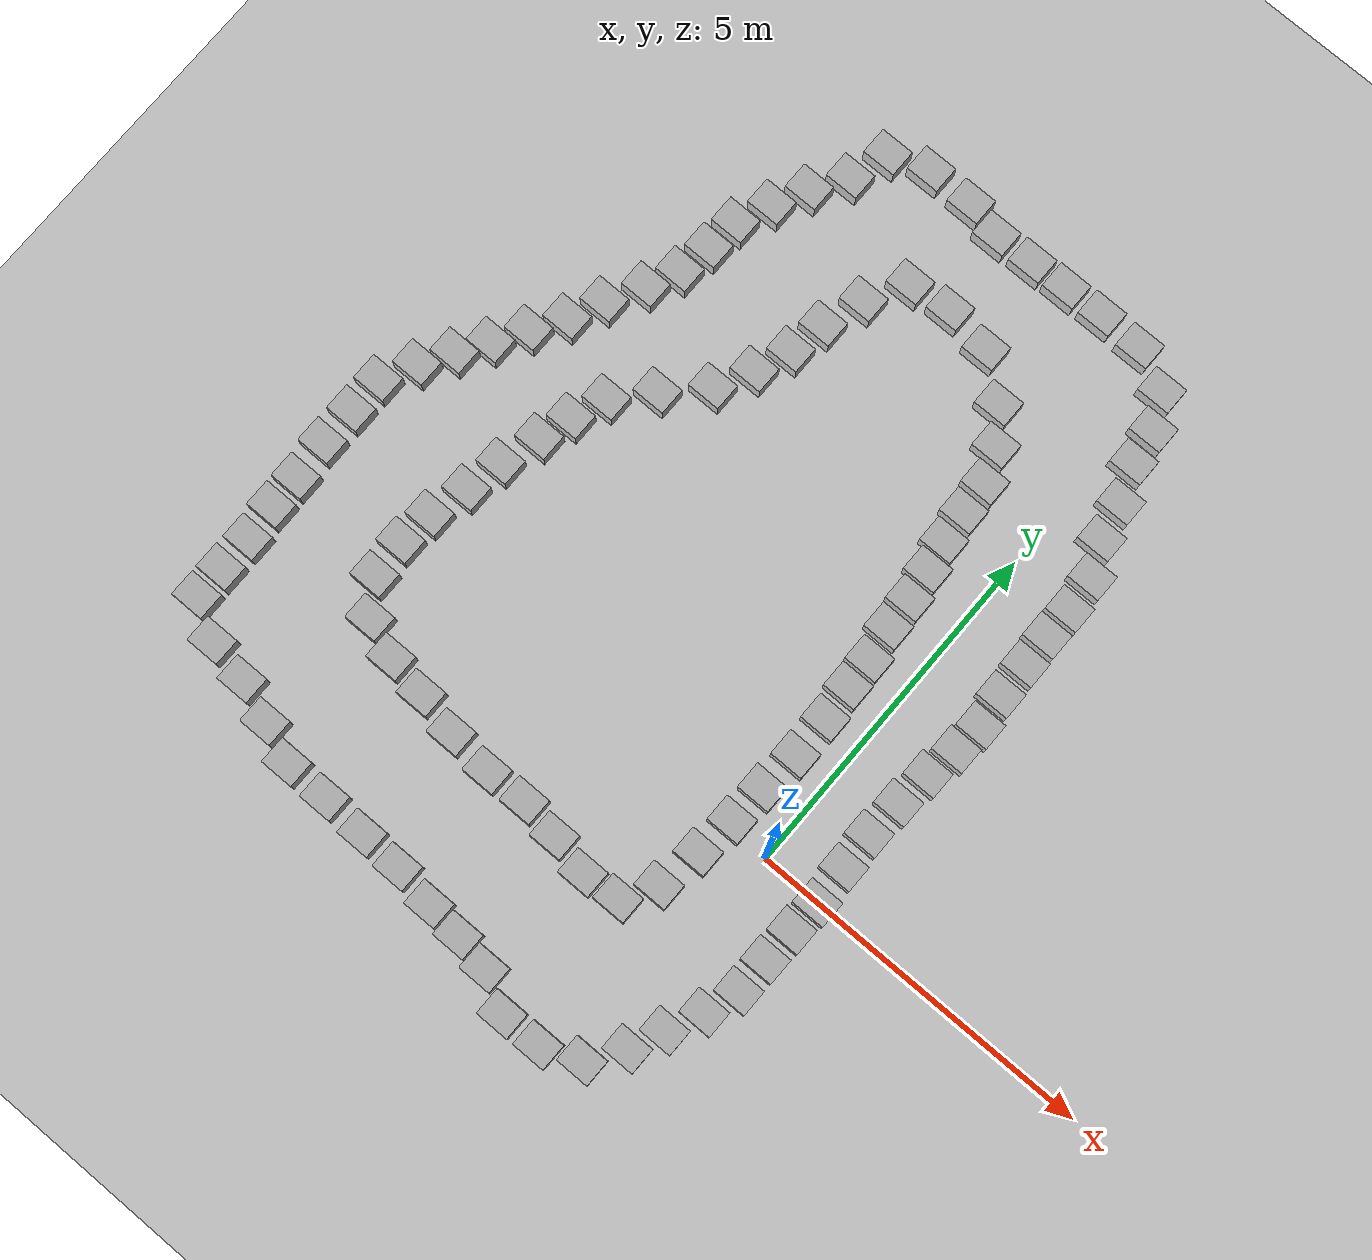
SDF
<sdf version='1.10'>
  <world name='empty'>
    <physics name='1ms' type='ignored'>
      <max_step_size>0.001</max_step_size>
      <real_time_factor>1</real_time_factor>
      <real_time_update_rate>1000</real_time_update_rate>
    </physics>
    <plugin name='gz::sim::systems::Physics' filename='gz-sim-physics-system'/>
    <plugin name='gz::sim::systems::UserCommands' filename='gz-sim-user-commands-system'/>
    <plugin name='gz::sim::systems::SceneBroadcaster' filename='gz-sim-scene-broadcaster-system'/>
    <plugin name='gz::sim::systems::Contact' filename='gz-sim-contact-system'/>
    <gravity>0 0 -9.8000000000000007</gravity>
    <magnetic_field>5.5644999999999998e-06 2.2875799999999999e-05 -4.2388400000000002e-05</magnetic_field>
    <atmosphere type='adiabatic'/>
    <scene>
      <ambient>0.400000006 0.400000006 0.400000006 1</ambient>
      <background>0.699999988 0.699999988 0.699999988 1</background>
      <shadows>true</shadows>
    </scene>
    <model name='ground_plane'>
      <static>true</static>
      <link name='link'>
        <collision name='collision'>
          <geometry>
            <plane>
              <normal>0 0 1</normal>
              <size>100 100</size>
            </plane>
          </geometry>
          <surface>
            <friction>
              <ode/>
            </friction>
            <bounce/>
            <contact/>
          </surface>
        </collision>
        <visual name='visual'>
          <geometry>
            <plane>
              <normal>0 0 1</normal>
              <size>100 100</size>
            </plane>
          </geometry>
          <material>
            <ambient>0.800000012 0.800000012 0.800000012 1</ambient>
            <diffuse>0.800000012 0.800000012 0.800000012 1</diffuse>
            <specular>0.800000012 0.800000012 0.800000012 1</specular>
          </material>
        </visual>
        <pose>0 0 0 0 0 0</pose>
        <inertial>
          <pose>0 0 0 0 0 0</pose>
          <mass>1</mass>
          <inertia>
            <ixx>1</ixx>
            <ixy>0</ixy>
            <ixz>0</ixz>
            <iyy>1</iyy>
            <iyz>0</iyz>
            <izz>1</izz>
          </inertia>
        </inertial>
        <enable_wind>false</enable_wind>
      </link>
      <pose>0 0 0 0 0 0</pose>
      <self_collide>false</self_collide>
    </model>
    <model name='cardboard_box'>
      <pose>0.85478054980913054 -0.014551958283302554 0.14999943493130527 -2.4298152294027702e-19 6.8969971186888291e-19 1.2039838720076909e-19</pose>
      <link name='link'>
        <inertial>
          <mass>2</mass>
          <inertia>
            <ixx>0.041666666999999998</ixx>
            <ixy>0</ixy>
            <ixz>0</ixz>
            <iyy>0.056666666999999997</iyy>
            <iyz>0</iyz>
            <izz>0.068333332999999996</izz>
          </inertia>
          <pose>0 0 0 0 0 0</pose>
        </inertial>
        <collision name='collision'>
          <geometry>
            <box>
              <size>0.5 0.40000000000000002 0.29999999999999999</size>
            </box>
          </geometry>
          <surface>
            <friction>
              <ode>
                <mu>1</mu>
                <mu2>1</mu2>
              </ode>
            </friction>
            <contact>
              <ode>
                <kp>10000000</kp>
                <kd>1</kd>
                <min_depth>0.001</min_depth>
                <max_vel>0.10000000000000001</max_vel>
              </ode>
            </contact>
            <bounce/>
          </surface>
        </collision>
        <visual name='visual'>
          <pose>0 0 -0.14999999999999999 0 0 0</pose>
          <geometry>
            <mesh>
              <uri>file:///home/szu/slash_ws/src/slash_sim/gz_models/cardboard_box/model://cardboard_box/meshes/cardboard_box.dae</uri>
              <scale>1.2593189600000001 1.0074551679999999 0.75559137600000004</scale>
            </mesh>
          </geometry>
        </visual>
        <pose>0 0 0 0 0 0</pose>
        <enable_wind>false</enable_wind>
      </link>
      <static>false</static>
      <self_collide>false</self_collide>
    </model>
    <model name='cardboard_box_2'>
      <pose>0.82918823358013261 -0.48284581720282427 0.14999943526777965 1.468051330599653e-18 -4.7075442468869343e-19 -1.1483520386083747e-20</pose>
      <link name='link'>
        <inertial>
          <mass>2</mass>
          <inertia>
            <ixx>0.041666666999999998</ixx>
            <ixy>0</ixy>
            <ixz>0</ixz>
            <iyy>0.056666666999999997</iyy>
            <iyz>0</iyz>
            <izz>0.068333332999999996</izz>
          </inertia>
        </inertial>
        <collision name='collision'>
          <geometry>
            <box>
              <size>0.5 0.40000000000000002 0.29999999999999999</size>
            </box>
          </geometry>
          <surface>
            <friction>
              <ode>
                <mu>1</mu>
                <mu2>1</mu2>
              </ode>
            </friction>
            <contact>
              <ode>
                <kp>10000000</kp>
                <kd>1</kd>
                <min_depth>0.001</min_depth>
                <max_vel>0.10000000000000001</max_vel>
              </ode>
            </contact>
            <bounce/>
          </surface>
        </collision>
        <visual name='visual'>
          <pose>0 0 -0.14999999999999999 0 0 0</pose>
          <geometry>
            <mesh>
              <uri>file:///home/szu/slash_ws/src/slash_sim/gz_models/cardboard_box/model://cardboard_box/meshes/cardboard_box.dae</uri>
              <scale>1.2593189600000001 1.0074551679999999 0.75559137600000004</scale>
            </mesh>
          </geometry>
        </visual>
      </link>
      <static>false</static>
      <self_collide>false</self_collide>
    </model>
    <model name='cardboard_box_1'>
      <pose>0.81471989938882383 -0.97593307698761844 0.14999900262897667 -2.4340092493284308e-19 6.9279252550571232e-19 1.2027156982183783e-19</pose>
      <link name='link'>
        <inertial>
          <mass>2</mass>
          <inertia>
            <ixx>0.041666666999999998</ixx>
            <ixy>0</ixy>
            <ixz>0</ixz>
            <iyy>0.056666666999999997</iyy>
            <iyz>0</iyz>
            <izz>0.068333332999999996</izz>
          </inertia>
        </inertial>
        <collision name='collision'>
          <geometry>
            <box>
              <size>0.5 0.40000000000000002 0.29999999999999999</size>
            </box>
          </geometry>
          <surface>
            <friction>
              <ode>
                <mu>1</mu>
                <mu2>1</mu2>
              </ode>
            </friction>
            <contact>
              <ode>
                <kp>10000000</kp>
                <kd>1</kd>
                <min_depth>0.001</min_depth>
                <max_vel>0.10000000000000001</max_vel>
              </ode>
            </contact>
            <bounce/>
          </surface>
        </collision>
        <visual name='visual'>
          <pose>0 0 -0.14999999999999999 0 0 0</pose>
          <geometry>
            <mesh>
              <uri>file:///home/szu/slash_ws/src/slash_sim/gz_models/cardboard_box/model://cardboard_box/meshes/cardboard_box.dae</uri>
              <scale>1.2593189600000001 1.0074551679999999 0.75559137600000004</scale>
            </mesh>
          </geometry>
        </visual>
      </link>
      <static>false</static>
      <self_collide>false</self_collide>
    </model>
    <model name='cardboard_box_3'>
      <pose>0.80992011127847019 -1.4853921208673166 0.14999900262897667 -2.4340092493284308e-19 6.9279252550571232e-19 1.2027156982183783e-19</pose>
      <link name='link'>
        <inertial>
          <mass>2</mass>
          <inertia>
            <ixx>0.041666666999999998</ixx>
            <ixy>0</ixy>
            <ixz>0</ixz>
            <iyy>0.056666666999999997</iyy>
            <iyz>0</iyz>
            <izz>0.068333332999999996</izz>
          </inertia>
        </inertial>
        <collision name='collision'>
          <geometry>
            <box>
              <size>0.5 0.40000000000000002 0.29999999999999999</size>
            </box>
          </geometry>
          <surface>
            <friction>
              <ode>
                <mu>1</mu>
                <mu2>1</mu2>
              </ode>
            </friction>
            <contact>
              <ode>
                <kp>10000000</kp>
                <kd>1</kd>
                <min_depth>0.001</min_depth>
                <max_vel>0.10000000000000001</max_vel>
              </ode>
            </contact>
            <bounce/>
          </surface>
        </collision>
        <visual name='visual'>
          <pose>0 0 -0.14999999999999999 0 0 0</pose>
          <geometry>
            <mesh>
              <uri>file:///home/szu/slash_ws/src/slash_sim/gz_models/cardboard_box/model://cardboard_box/meshes/cardboard_box.dae</uri>
              <scale>1.2593189600000001 1.0074551679999999 0.75559137600000004</scale>
            </mesh>
          </geometry>
        </visual>
      </link>
      <static>false</static>
      <self_collide>false</self_collide>
    </model>
    <model name='cardboard_box_4'>
      <pose>0.65241971092314321 -1.9664045753572796 0.14999900262897667 -2.4340092493284308e-19 6.9279252550571232e-19 1.2027156982183783e-19</pose>
      <link name='link'>
        <inertial>
          <mass>2</mass>
          <inertia>
            <ixx>0.041666666999999998</ixx>
            <ixy>0</ixy>
            <ixz>0</ixz>
            <iyy>0.056666666999999997</iyy>
            <iyz>0</iyz>
            <izz>0.068333332999999996</izz>
          </inertia>
        </inertial>
        <collision name='collision'>
          <geometry>
            <box>
              <size>0.5 0.40000000000000002 0.29999999999999999</size>
            </box>
          </geometry>
          <surface>
            <friction>
              <ode>
                <mu>1</mu>
                <mu2>1</mu2>
              </ode>
            </friction>
            <contact>
              <ode>
                <kp>10000000</kp>
                <kd>1</kd>
                <min_depth>0.001</min_depth>
                <max_vel>0.10000000000000001</max_vel>
              </ode>
            </contact>
            <bounce/>
          </surface>
        </collision>
        <visual name='visual'>
          <pose>0 0 -0.14999999999999999 0 0 0</pose>
          <geometry>
            <mesh>
              <uri>file:///home/szu/slash_ws/src/slash_sim/gz_models/cardboard_box/model://cardboard_box/meshes/cardboard_box.dae</uri>
              <scale>1.2593189600000001 1.0074551679999999 0.75559137600000004</scale>
            </mesh>
          </geometry>
        </visual>
      </link>
      <static>false</static>
      <self_collide>false</self_collide>
    </model>
    <model name='cardboard_box_5'>
      <pose>0.42300615484042769 -2.4551073116075139 0.14999900262897667 -2.3882218747492828e-19 7.0060126461846494e-19 1.2009065340730555e-19</pose>
      <link name='link'>
        <inertial>
          <mass>2</mass>
          <inertia>
            <ixx>0.041666666999999998</ixx>
            <ixy>0</ixy>
            <ixz>0</ixz>
            <iyy>0.056666666999999997</iyy>
            <iyz>0</iyz>
            <izz>0.068333332999999996</izz>
          </inertia>
        </inertial>
        <collision name='collision'>
          <geometry>
            <box>
              <size>0.5 0.40000000000000002 0.29999999999999999</size>
            </box>
          </geometry>
          <surface>
            <friction>
              <ode>
                <mu>1</mu>
                <mu2>1</mu2>
              </ode>
            </friction>
            <contact>
              <ode>
                <kp>10000000</kp>
                <kd>1</kd>
                <min_depth>0.001</min_depth>
                <max_vel>0.10000000000000001</max_vel>
              </ode>
            </contact>
            <bounce/>
          </surface>
        </collision>
        <visual name='visual'>
          <pose>0 0 -0.14999999999999999 0 0 0</pose>
          <geometry>
            <mesh>
              <uri>file:///home/szu/slash_ws/src/slash_sim/gz_models/cardboard_box/model://cardboard_box/meshes/cardboard_box.dae</uri>
              <scale>1.2593189600000001 1.0074551679999999 0.75559137600000004</scale>
            </mesh>
          </geometry>
        </visual>
      </link>
      <static>false</static>
      <self_collide>false</self_collide>
    </model>
    <model name='cardboard_box_6'>
      <pose>0.21282287062685212 -2.925903574118673 0.14999900262897667 -2.3882218747492828e-19 7.0060126461846494e-19 1.2009065340730555e-19</pose>
      <link name='link'>
        <inertial>
          <mass>2</mass>
          <inertia>
            <ixx>0.041666666999999998</ixx>
            <ixy>0</ixy>
            <ixz>0</ixz>
            <iyy>0.056666666999999997</iyy>
            <iyz>0</iyz>
            <izz>0.068333332999999996</izz>
          </inertia>
        </inertial>
        <collision name='collision'>
          <geometry>
            <box>
              <size>0.5 0.40000000000000002 0.29999999999999999</size>
            </box>
          </geometry>
          <surface>
            <friction>
              <ode>
                <mu>1</mu>
                <mu2>1</mu2>
              </ode>
            </friction>
            <contact>
              <ode>
                <kp>10000000</kp>
                <kd>1</kd>
                <min_depth>0.001</min_depth>
                <max_vel>0.10000000000000001</max_vel>
              </ode>
            </contact>
            <bounce/>
          </surface>
        </collision>
        <visual name='visual'>
          <pose>0 0 -0.14999999999999999 0 0 0</pose>
          <geometry>
            <mesh>
              <uri>file:///home/szu/slash_ws/src/slash_sim/gz_models/cardboard_box/model://cardboard_box/meshes/cardboard_box.dae</uri>
              <scale>1.2593189600000001 1.0074551679999999 0.75559137600000004</scale>
            </mesh>
          </geometry>
        </visual>
      </link>
      <static>false</static>
      <self_collide>false</self_collide>
    </model>
    <model name='cardboard_box_7'>
      <pose>-0.11863343668581763 -3.3982007797930551 0.14999900262897667 -2.4848020336017288e-19 6.8408961370786333e-19 1.2063749059190658e-19</pose>
      <link name='link'>
        <inertial>
          <mass>2</mass>
          <inertia>
            <ixx>0.041666666999999998</ixx>
            <ixy>0</ixy>
            <ixz>0</ixz>
            <iyy>0.056666666999999997</iyy>
            <iyz>0</iyz>
            <izz>0.068333332999999996</izz>
          </inertia>
        </inertial>
        <collision name='collision'>
          <geometry>
            <box>
              <size>0.5 0.40000000000000002 0.29999999999999999</size>
            </box>
          </geometry>
          <surface>
            <friction>
              <ode>
                <mu>1</mu>
                <mu2>1</mu2>
              </ode>
            </friction>
            <contact>
              <ode>
                <kp>10000000</kp>
                <kd>1</kd>
                <min_depth>0.001</min_depth>
                <max_vel>0.10000000000000001</max_vel>
              </ode>
            </contact>
            <bounce/>
          </surface>
        </collision>
        <visual name='visual'>
          <pose>0 0 -0.14999999999999999 0 0 0</pose>
          <geometry>
            <mesh>
              <uri>file:///home/szu/slash_ws/src/slash_sim/gz_models/cardboard_box/model://cardboard_box/meshes/cardboard_box.dae</uri>
              <scale>1.2593189600000001 1.0074551679999999 0.75559137600000004</scale>
            </mesh>
          </geometry>
        </visual>
      </link>
      <static>false</static>
      <self_collide>false</self_collide>
    </model>
    <model name='cardboard_box_8'>
      <pose>-0.65943831398405628 -3.6029109999164235 0.14999900262897667 -2.3882218747492828e-19 7.0060126461846494e-19 1.2009065340730555e-19</pose>
      <link name='link'>
        <inertial>
          <mass>2</mass>
          <inertia>
            <ixx>0.041666666999999998</ixx>
            <ixy>0</ixy>
            <ixz>0</ixz>
            <iyy>0.056666666999999997</iyy>
            <iyz>0</iyz>
            <izz>0.068333332999999996</izz>
          </inertia>
        </inertial>
        <collision name='collision'>
          <geometry>
            <box>
              <size>0.5 0.40000000000000002 0.29999999999999999</size>
            </box>
          </geometry>
          <surface>
            <friction>
              <ode>
                <mu>1</mu>
                <mu2>1</mu2>
              </ode>
            </friction>
            <contact>
              <ode>
                <kp>10000000</kp>
                <kd>1</kd>
                <min_depth>0.001</min_depth>
                <max_vel>0.10000000000000001</max_vel>
              </ode>
            </contact>
            <bounce/>
          </surface>
        </collision>
        <visual name='visual'>
          <pose>0 0 -0.14999999999999999 0 0 0</pose>
          <geometry>
            <mesh>
              <uri>file:///home/szu/slash_ws/src/slash_sim/gz_models/cardboard_box/model://cardboard_box/meshes/cardboard_box.dae</uri>
              <scale>1.2593189600000001 1.0074551679999999 0.75559137600000004</scale>
            </mesh>
          </geometry>
        </visual>
      </link>
      <static>false</static>
      <self_collide>false</self_collide>
    </model>
    <model name='cardboard_box_9'>
      <pose>-1.2508540111511406 -3.6073572218996501 0.14999900262897667 -2.3882218747492828e-19 7.0060126461846494e-19 1.2009065340730555e-19</pose>
      <link name='link'>
        <inertial>
          <mass>2</mass>
          <inertia>
            <ixx>0.041666666999999998</ixx>
            <ixy>0</ixy>
            <ixz>0</ixz>
            <iyy>0.056666666999999997</iyy>
            <iyz>0</iyz>
            <izz>0.068333332999999996</izz>
          </inertia>
        </inertial>
        <collision name='collision'>
          <geometry>
            <box>
              <size>0.5 0.40000000000000002 0.29999999999999999</size>
            </box>
          </geometry>
          <surface>
            <friction>
              <ode>
                <mu>1</mu>
                <mu2>1</mu2>
              </ode>
            </friction>
            <contact>
              <ode>
                <kp>10000000</kp>
                <kd>1</kd>
                <min_depth>0.001</min_depth>
                <max_vel>0.10000000000000001</max_vel>
              </ode>
            </contact>
            <bounce/>
          </surface>
        </collision>
        <visual name='visual'>
          <pose>0 0 -0.14999999999999999 0 0 0</pose>
          <geometry>
            <mesh>
              <uri>file:///home/szu/slash_ws/src/slash_sim/gz_models/cardboard_box/model://cardboard_box/meshes/cardboard_box.dae</uri>
              <scale>1.2593189600000001 1.0074551679999999 0.75559137600000004</scale>
            </mesh>
          </geometry>
        </visual>
      </link>
      <static>false</static>
      <self_collide>false</self_collide>
    </model>
    <model name='cardboard_box_10'>
      <pose>-1.7887590245711507 -3.3225877841246536 0.14999900262897667 -2.3882218747492828e-19 7.0060126461846494e-19 1.2009065340730555e-19</pose>
      <link name='link'>
        <inertial>
          <mass>2</mass>
          <inertia>
            <ixx>0.041666666999999998</ixx>
            <ixy>0</ixy>
            <ixz>0</ixz>
            <iyy>0.056666666999999997</iyy>
            <iyz>0</iyz>
            <izz>0.068333332999999996</izz>
          </inertia>
        </inertial>
        <collision name='collision'>
          <geometry>
            <box>
              <size>0.5 0.40000000000000002 0.29999999999999999</size>
            </box>
          </geometry>
          <surface>
            <friction>
              <ode>
                <mu>1</mu>
                <mu2>1</mu2>
              </ode>
            </friction>
            <contact>
              <ode>
                <kp>10000000</kp>
                <kd>1</kd>
                <min_depth>0.001</min_depth>
                <max_vel>0.10000000000000001</max_vel>
              </ode>
            </contact>
            <bounce/>
          </surface>
        </collision>
        <visual name='visual'>
          <pose>0 0 -0.14999999999999999 0 0 0</pose>
          <geometry>
            <mesh>
              <uri>file:///home/szu/slash_ws/src/slash_sim/gz_models/cardboard_box/model://cardboard_box/meshes/cardboard_box.dae</uri>
              <scale>1.2593189600000001 1.0074551679999999 0.75559137600000004</scale>
            </mesh>
          </geometry>
        </visual>
      </link>
      <static>false</static>
      <self_collide>false</self_collide>
    </model>
    <model name='cardboard_box_11'>
      <pose>-2.3112200243576413 -3.2260066538424192 0.14999900262897667 -2.3882218747492828e-19 7.0060126461846494e-19 1.2009065340730555e-19</pose>
      <link name='link'>
        <inertial>
          <mass>2</mass>
          <inertia>
            <ixx>0.041666666999999998</ixx>
            <ixy>0</ixy>
            <ixz>0</ixz>
            <iyy>0.056666666999999997</iyy>
            <iyz>0</iyz>
            <izz>0.068333332999999996</izz>
          </inertia>
        </inertial>
        <collision name='collision'>
          <geometry>
            <box>
              <size>0.5 0.40000000000000002 0.29999999999999999</size>
            </box>
          </geometry>
          <surface>
            <friction>
              <ode>
                <mu>1</mu>
                <mu2>1</mu2>
              </ode>
            </friction>
            <contact>
              <ode>
                <kp>10000000</kp>
                <kd>1</kd>
                <min_depth>0.001</min_depth>
                <max_vel>0.10000000000000001</max_vel>
              </ode>
            </contact>
            <bounce/>
          </surface>
        </collision>
        <visual name='visual'>
          <pose>0 0 -0.14999999999999999 0 0 0</pose>
          <geometry>
            <mesh>
              <uri>file:///home/szu/slash_ws/src/slash_sim/gz_models/cardboard_box/model://cardboard_box/meshes/cardboard_box.dae</uri>
              <scale>1.2593189600000001 1.0074551679999999 0.75559137600000004</scale>
            </mesh>
          </geometry>
        </visual>
      </link>
      <static>false</static>
      <self_collide>false</self_collide>
    </model>
    <model name='cardboard_box_12'>
      <pose>-2.8382995273990406 -3.1674697978062643 0.14999900262897667 -2.3882218747492828e-19 7.0060126461846494e-19 1.2009065340730555e-19</pose>
      <link name='link'>
        <inertial>
          <mass>2</mass>
          <inertia>
            <ixx>0.041666666999999998</ixx>
            <ixy>0</ixy>
            <ixz>0</ixz>
            <iyy>0.056666666999999997</iyy>
            <iyz>0</iyz>
            <izz>0.068333332999999996</izz>
          </inertia>
        </inertial>
        <collision name='collision'>
          <geometry>
            <box>
              <size>0.5 0.40000000000000002 0.29999999999999999</size>
            </box>
          </geometry>
          <surface>
            <friction>
              <ode>
                <mu>1</mu>
                <mu2>1</mu2>
              </ode>
            </friction>
            <contact>
              <ode>
                <kp>10000000</kp>
                <kd>1</kd>
                <min_depth>0.001</min_depth>
                <max_vel>0.10000000000000001</max_vel>
              </ode>
            </contact>
            <bounce/>
          </surface>
        </collision>
        <visual name='visual'>
          <pose>0 0 -0.14999999999999999 0 0 0</pose>
          <geometry>
            <mesh>
              <uri>file:///home/szu/slash_ws/src/slash_sim/gz_models/cardboard_box/model://cardboard_box/meshes/cardboard_box.dae</uri>
              <scale>1.2593189600000001 1.0074551679999999 0.75559137600000004</scale>
            </mesh>
          </geometry>
        </visual>
      </link>
      <static>false</static>
      <self_collide>false</self_collide>
    </model>
    <model name='cardboard_box_13'>
      <pose>-3.4479739644392979 -3.0739339302603668 0.14999900262897667 -2.3882218747492828e-19 7.0060126461846494e-19 1.2009065340730555e-19</pose>
      <link name='link'>
        <inertial>
          <mass>2</mass>
          <inertia>
            <ixx>0.041666666999999998</ixx>
            <ixy>0</ixy>
            <ixz>0</ixz>
            <iyy>0.056666666999999997</iyy>
            <iyz>0</iyz>
            <izz>0.068333332999999996</izz>
          </inertia>
        </inertial>
        <collision name='collision'>
          <geometry>
            <box>
              <size>0.5 0.40000000000000002 0.29999999999999999</size>
            </box>
          </geometry>
          <surface>
            <friction>
              <ode>
                <mu>1</mu>
                <mu2>1</mu2>
              </ode>
            </friction>
            <contact>
              <ode>
                <kp>10000000</kp>
                <kd>1</kd>
                <min_depth>0.001</min_depth>
                <max_vel>0.10000000000000001</max_vel>
              </ode>
            </contact>
            <bounce/>
          </surface>
        </collision>
        <visual name='visual'>
          <pose>0 0 -0.14999999999999999 0 0 0</pose>
          <geometry>
            <mesh>
              <uri>file:///home/szu/slash_ws/src/slash_sim/gz_models/cardboard_box/model://cardboard_box/meshes/cardboard_box.dae</uri>
              <scale>1.2593189600000001 1.0074551679999999 0.75559137600000004</scale>
            </mesh>
          </geometry>
        </visual>
      </link>
      <static>false</static>
      <self_collide>false</self_collide>
    </model>
    <model name='cardboard_box_14'>
      <pose>-4.0666289461102183 -3.0440014481805937 0.14999900262897667 -2.3882218747492828e-19 7.0060126461846494e-19 1.2009065340730555e-19</pose>
      <link name='link'>
        <inertial>
          <mass>2</mass>
          <inertia>
            <ixx>0.041666666999999998</ixx>
            <ixy>0</ixy>
            <ixz>0</ixz>
            <iyy>0.056666666999999997</iyy>
            <iyz>0</iyz>
            <izz>0.068333332999999996</izz>
          </inertia>
        </inertial>
        <collision name='collision'>
          <geometry>
            <box>
              <size>0.5 0.40000000000000002 0.29999999999999999</size>
            </box>
          </geometry>
          <surface>
            <friction>
              <ode>
                <mu>1</mu>
                <mu2>1</mu2>
              </ode>
            </friction>
            <contact>
              <ode>
                <kp>10000000</kp>
                <kd>1</kd>
                <min_depth>0.001</min_depth>
                <max_vel>0.10000000000000001</max_vel>
              </ode>
            </contact>
            <bounce/>
          </surface>
        </collision>
        <visual name='visual'>
          <pose>0 0 -0.14999999999999999 0 0 0</pose>
          <geometry>
            <mesh>
              <uri>file:///home/szu/slash_ws/src/slash_sim/gz_models/cardboard_box/model://cardboard_box/meshes/cardboard_box.dae</uri>
              <scale>1.2593189600000001 1.0074551679999999 0.75559137600000004</scale>
            </mesh>
          </geometry>
        </visual>
      </link>
      <static>false</static>
      <self_collide>false</self_collide>
    </model>
    <model name='cardboard_box_15'>
      <pose>-4.7268743832117153 -3.0079390506296462 0.14999900262897667 -2.3882218747492828e-19 7.0060126461846494e-19 1.2009065340730555e-19</pose>
      <link name='link'>
        <inertial>
          <mass>2</mass>
          <inertia>
            <ixx>0.041666666999999998</ixx>
            <ixy>0</ixy>
            <ixz>0</ixz>
            <iyy>0.056666666999999997</iyy>
            <iyz>0</iyz>
            <izz>0.068333332999999996</izz>
          </inertia>
        </inertial>
        <collision name='collision'>
          <geometry>
            <box>
              <size>0.5 0.40000000000000002 0.29999999999999999</size>
            </box>
          </geometry>
          <surface>
            <friction>
              <ode>
                <mu>1</mu>
                <mu2>1</mu2>
              </ode>
            </friction>
            <contact>
              <ode>
                <kp>10000000</kp>
                <kd>1</kd>
                <min_depth>0.001</min_depth>
                <max_vel>0.10000000000000001</max_vel>
              </ode>
            </contact>
            <bounce/>
          </surface>
        </collision>
        <visual name='visual'>
          <pose>0 0 -0.14999999999999999 0 0 0</pose>
          <geometry>
            <mesh>
              <uri>file:///home/szu/slash_ws/src/slash_sim/gz_models/cardboard_box/model://cardboard_box/meshes/cardboard_box.dae</uri>
              <scale>1.2593189600000001 1.0074551679999999 0.75559137600000004</scale>
            </mesh>
          </geometry>
        </visual>
      </link>
      <static>false</static>
      <self_collide>false</self_collide>
    </model>
    <model name='cardboard_box_16'>
      <pose>-5.3803726022670695 -2.9915414197180037 0.14999900262897667 -2.3882218747492828e-19 7.0060126461846494e-19 1.2009065340730555e-19</pose>
      <link name='link'>
        <inertial>
          <mass>2</mass>
          <inertia>
            <ixx>0.041666666999999998</ixx>
            <ixy>0</ixy>
            <ixz>0</ixz>
            <iyy>0.056666666999999997</iyy>
            <iyz>0</iyz>
            <izz>0.068333332999999996</izz>
          </inertia>
        </inertial>
        <collision name='collision'>
          <geometry>
            <box>
              <size>0.5 0.40000000000000002 0.29999999999999999</size>
            </box>
          </geometry>
          <surface>
            <friction>
              <ode>
                <mu>1</mu>
                <mu2>1</mu2>
              </ode>
            </friction>
            <contact>
              <ode>
                <kp>10000000</kp>
                <kd>1</kd>
                <min_depth>0.001</min_depth>
                <max_vel>0.10000000000000001</max_vel>
              </ode>
            </contact>
            <bounce/>
          </surface>
        </collision>
        <visual name='visual'>
          <pose>0 0 -0.14999999999999999 0 0 0</pose>
          <geometry>
            <mesh>
              <uri>file:///home/szu/slash_ws/src/slash_sim/gz_models/cardboard_box/model://cardboard_box/meshes/cardboard_box.dae</uri>
              <scale>1.2593189600000001 1.0074551679999999 0.75559137600000004</scale>
            </mesh>
          </geometry>
        </visual>
      </link>
      <static>false</static>
      <self_collide>false</self_collide>
    </model>
    <model name='cardboard_box_17'>
      <pose>-5.9379788822694248 -2.779304179914567 0.14999900262897667 -2.3882218747492828e-19 7.0060126461846494e-19 1.2009065340730555e-19</pose>
      <link name='link'>
        <inertial>
          <mass>2</mass>
          <inertia>
            <ixx>0.041666666999999998</ixx>
            <ixy>0</ixy>
            <ixz>0</ixz>
            <iyy>0.056666666999999997</iyy>
            <iyz>0</iyz>
            <izz>0.068333332999999996</izz>
          </inertia>
        </inertial>
        <collision name='collision'>
          <geometry>
            <box>
              <size>0.5 0.40000000000000002 0.29999999999999999</size>
            </box>
          </geometry>
          <surface>
            <friction>
              <ode>
                <mu>1</mu>
                <mu2>1</mu2>
              </ode>
            </friction>
            <contact>
              <ode>
                <kp>10000000</kp>
                <kd>1</kd>
                <min_depth>0.001</min_depth>
                <max_vel>0.10000000000000001</max_vel>
              </ode>
            </contact>
            <bounce/>
          </surface>
        </collision>
        <visual name='visual'>
          <pose>0 0 -0.14999999999999999 0 0 0</pose>
          <geometry>
            <mesh>
              <uri>file:///home/szu/slash_ws/src/slash_sim/gz_models/cardboard_box/model://cardboard_box/meshes/cardboard_box.dae</uri>
              <scale>1.2593189600000001 1.0074551679999999 0.75559137600000004</scale>
            </mesh>
          </geometry>
        </visual>
      </link>
      <static>false</static>
      <self_collide>false</self_collide>
    </model>
    <model name='cardboard_box_18'>
      <pose>-6.5225413445512554 -2.5643485998146858 0.14999900262897667 -2.3882218747492828e-19 7.0060126461846494e-19 1.2009065340730555e-19</pose>
      <link name='link'>
        <inertial>
          <mass>2</mass>
          <inertia>
            <ixx>0.041666666999999998</ixx>
            <ixy>0</ixy>
            <ixz>0</ixz>
            <iyy>0.056666666999999997</iyy>
            <iyz>0</iyz>
            <izz>0.068333332999999996</izz>
          </inertia>
        </inertial>
        <collision name='collision'>
          <geometry>
            <box>
              <size>0.5 0.40000000000000002 0.29999999999999999</size>
            </box>
          </geometry>
          <surface>
            <friction>
              <ode>
                <mu>1</mu>
                <mu2>1</mu2>
              </ode>
            </friction>
            <contact>
              <ode>
                <kp>10000000</kp>
                <kd>1</kd>
                <min_depth>0.001</min_depth>
                <max_vel>0.10000000000000001</max_vel>
              </ode>
            </contact>
            <bounce/>
          </surface>
        </collision>
        <visual name='visual'>
          <pose>0 0 -0.14999999999999999 0 0 0</pose>
          <geometry>
            <mesh>
              <uri>file:///home/szu/slash_ws/src/slash_sim/gz_models/cardboard_box/model://cardboard_box/meshes/cardboard_box.dae</uri>
              <scale>1.2593189600000001 1.0074551679999999 0.75559137600000004</scale>
            </mesh>
          </geometry>
        </visual>
      </link>
      <static>false</static>
      <self_collide>false</self_collide>
    </model>
    <model name='cardboard_box_19'>
      <pose>-7.1408973483773224 -2.4413015255535058 0.149999987441674 5.6848285000596318e-13 3.0140203723890403e-08 -4.5919229407915538e-06</pose>
      <link name='link'>
        <inertial>
          <mass>2</mass>
          <inertia>
            <ixx>0.041666666999999998</ixx>
            <ixy>0</ixy>
            <ixz>0</ixz>
            <iyy>0.056666666999999997</iyy>
            <iyz>0</iyz>
            <izz>0.068333332999999996</izz>
          </inertia>
        </inertial>
        <collision name='collision'>
          <geometry>
            <box>
              <size>0.5 0.40000000000000002 0.29999999999999999</size>
            </box>
          </geometry>
          <surface>
            <friction>
              <ode>
                <mu>1</mu>
                <mu2>1</mu2>
              </ode>
            </friction>
            <contact>
              <ode>
                <kp>10000000</kp>
                <kd>1</kd>
                <min_depth>0.001</min_depth>
                <max_vel>0.10000000000000001</max_vel>
              </ode>
            </contact>
            <bounce/>
          </surface>
        </collision>
        <visual name='visual'>
          <pose>0 0 -0.14999999999999999 0 0 0</pose>
          <geometry>
            <mesh>
              <uri>file:///home/szu/slash_ws/src/slash_sim/gz_models/cardboard_box/model://cardboard_box/meshes/cardboard_box.dae</uri>
              <scale>1.2593189600000001 1.0074551679999999 0.75559137600000004</scale>
            </mesh>
          </geometry>
        </visual>
      </link>
      <static>false</static>
      <self_collide>false</self_collide>
    </model>
    <model name='cardboard_box_21'>
      <pose>-7.6931963475884668 -1.662565945218375 0.14999900262897667 -2.4340092493284308e-19 6.9279252550571232e-19 1.2027156982183783e-19</pose>
      <link name='link'>
        <inertial>
          <mass>2</mass>
          <inertia>
            <ixx>0.041666666999999998</ixx>
            <ixy>0</ixy>
            <ixz>0</ixz>
            <iyy>0.056666666999999997</iyy>
            <iyz>0</iyz>
            <izz>0.068333332999999996</izz>
          </inertia>
        </inertial>
        <collision name='collision'>
          <geometry>
            <box>
              <size>0.5 0.40000000000000002 0.29999999999999999</size>
            </box>
          </geometry>
          <surface>
            <friction>
              <ode>
                <mu>1</mu>
                <mu2>1</mu2>
              </ode>
            </friction>
            <contact>
              <ode>
                <kp>10000000</kp>
                <kd>1</kd>
                <min_depth>0.001</min_depth>
                <max_vel>0.10000000000000001</max_vel>
              </ode>
            </contact>
            <bounce/>
          </surface>
        </collision>
        <visual name='visual'>
          <pose>0 0 -0.14999999999999999 0 0 0</pose>
          <geometry>
            <mesh>
              <uri>file:///home/szu/slash_ws/src/slash_sim/gz_models/cardboard_box/model://cardboard_box/meshes/cardboard_box.dae</uri>
              <scale>1.2593189600000001 1.0074551679999999 0.75559137600000004</scale>
            </mesh>
          </geometry>
        </visual>
      </link>
      <static>false</static>
      <self_collide>false</self_collide>
    </model>
    <model name='cardboard_box_20'>
      <pose>-7.6865004889883242 -2.130387934828323 0.14999900262897667 -2.4617464613720411e-19 6.9865286339511872e-19 1.2102648454319885e-19</pose>
      <link name='link'>
        <inertial>
          <mass>2</mass>
          <inertia>
            <ixx>0.041666666999999998</ixx>
            <ixy>0</ixy>
            <ixz>0</ixz>
            <iyy>0.056666666999999997</iyy>
            <iyz>0</iyz>
            <izz>0.068333332999999996</izz>
          </inertia>
        </inertial>
        <collision name='collision'>
          <geometry>
            <box>
              <size>0.5 0.40000000000000002 0.29999999999999999</size>
            </box>
          </geometry>
          <surface>
            <friction>
              <ode>
                <mu>1</mu>
                <mu2>1</mu2>
              </ode>
            </friction>
            <contact>
              <ode>
                <kp>10000000</kp>
                <kd>1</kd>
                <min_depth>0.001</min_depth>
                <max_vel>0.10000000000000001</max_vel>
              </ode>
            </contact>
            <bounce/>
          </surface>
        </collision>
        <visual name='visual'>
          <pose>0 0 -0.14999999999999999 0 0 0</pose>
          <geometry>
            <mesh>
              <uri>file:///home/szu/slash_ws/src/slash_sim/gz_models/cardboard_box/model://cardboard_box/meshes/cardboard_box.dae</uri>
              <scale>1.2593189600000001 1.0074551679999999 0.75559137600000004</scale>
            </mesh>
          </geometry>
        </visual>
      </link>
      <static>false</static>
      <self_collide>false</self_collide>
    </model>
    <model name='cardboard_box_22'>
      <pose>-7.6940470332278661 -1.1493551750067641 0.14999900262897667 -2.4340092493284308e-19 6.9279252550571232e-19 1.2027156982183783e-19</pose>
      <link name='link'>
        <inertial>
          <mass>2</mass>
          <inertia>
            <ixx>0.041666666999999998</ixx>
            <ixy>0</ixy>
            <ixz>0</ixz>
            <iyy>0.056666666999999997</iyy>
            <iyz>0</iyz>
            <izz>0.068333332999999996</izz>
          </inertia>
        </inertial>
        <collision name='collision'>
          <geometry>
            <box>
              <size>0.5 0.40000000000000002 0.29999999999999999</size>
            </box>
          </geometry>
          <surface>
            <friction>
              <ode>
                <mu>1</mu>
                <mu2>1</mu2>
              </ode>
            </friction>
            <contact>
              <ode>
                <kp>10000000</kp>
                <kd>1</kd>
                <min_depth>0.001</min_depth>
                <max_vel>0.10000000000000001</max_vel>
              </ode>
            </contact>
            <bounce/>
          </surface>
        </collision>
        <visual name='visual'>
          <pose>0 0 -0.14999999999999999 0 0 0</pose>
          <geometry>
            <mesh>
              <uri>file:///home/szu/slash_ws/src/slash_sim/gz_models/cardboard_box/model://cardboard_box/meshes/cardboard_box.dae</uri>
              <scale>1.2593189600000001 1.0074551679999999 0.75559137600000004</scale>
            </mesh>
          </geometry>
        </visual>
      </link>
      <static>false</static>
      <self_collide>false</self_collide>
    </model>
    <model name='cardboard_box_23'>
      <pose>-7.7438613160016532 -0.63811395418226091 0.14999900262897667 -2.2431381697928032e-19 6.9715337893438625e-19 1.2058972534000899e-19</pose>
      <link name='link'>
        <inertial>
          <mass>2</mass>
          <inertia>
            <ixx>0.041666666999999998</ixx>
            <ixy>0</ixy>
            <ixz>0</ixz>
            <iyy>0.056666666999999997</iyy>
            <iyz>0</iyz>
            <izz>0.068333332999999996</izz>
          </inertia>
        </inertial>
        <collision name='collision'>
          <geometry>
            <box>
              <size>0.5 0.40000000000000002 0.29999999999999999</size>
            </box>
          </geometry>
          <surface>
            <friction>
              <ode>
                <mu>1</mu>
                <mu2>1</mu2>
              </ode>
            </friction>
            <contact>
              <ode>
                <kp>10000000</kp>
                <kd>1</kd>
                <min_depth>0.001</min_depth>
                <max_vel>0.10000000000000001</max_vel>
              </ode>
            </contact>
            <bounce/>
          </surface>
        </collision>
        <visual name='visual'>
          <pose>0 0 -0.14999999999999999 0 0 0</pose>
          <geometry>
            <mesh>
              <uri>file:///home/szu/slash_ws/src/slash_sim/gz_models/cardboard_box/model://cardboard_box/meshes/cardboard_box.dae</uri>
              <scale>1.2593189600000001 1.0074551679999999 0.75559137600000004</scale>
            </mesh>
          </geometry>
        </visual>
      </link>
      <static>false</static>
      <self_collide>false</self_collide>
    </model>
    <model name='cardboard_box_24'>
      <pose>-7.7540243617888276 -0.15357185266683215 0.14999900262897667 -2.5080923996314153e-19 6.9013454270577445e-19 1.2087524920852755e-19</pose>
      <link name='link'>
        <inertial>
          <mass>2</mass>
          <inertia>
            <ixx>0.041666666999999998</ixx>
            <ixy>0</ixy>
            <ixz>0</ixz>
            <iyy>0.056666666999999997</iyy>
            <iyz>0</iyz>
            <izz>0.068333332999999996</izz>
          </inertia>
        </inertial>
        <collision name='collision'>
          <geometry>
            <box>
              <size>0.5 0.40000000000000002 0.29999999999999999</size>
            </box>
          </geometry>
          <surface>
            <friction>
              <ode>
                <mu>1</mu>
                <mu2>1</mu2>
              </ode>
            </friction>
            <contact>
              <ode>
                <kp>10000000</kp>
                <kd>1</kd>
                <min_depth>0.001</min_depth>
                <max_vel>0.10000000000000001</max_vel>
              </ode>
            </contact>
            <bounce/>
          </surface>
        </collision>
        <visual name='visual'>
          <pose>0 0 -0.14999999999999999 0 0 0</pose>
          <geometry>
            <mesh>
              <uri>file:///home/szu/slash_ws/src/slash_sim/gz_models/cardboard_box/model://cardboard_box/meshes/cardboard_box.dae</uri>
              <scale>1.2593189600000001 1.0074551679999999 0.75559137600000004</scale>
            </mesh>
          </geometry>
        </visual>
      </link>
      <static>false</static>
      <self_collide>false</self_collide>
    </model>
    <model name='cardboard_box_25'>
      <pose>-7.80474633593718 0.41818384150236687 0.14999900262897667 -2.5123466248672699e-19 6.9657739388306372e-19 1.209647203754103e-19</pose>
      <link name='link'>
        <inertial>
          <mass>2</mass>
          <inertia>
            <ixx>0.041666666999999998</ixx>
            <ixy>0</ixy>
            <ixz>0</ixz>
            <iyy>0.056666666999999997</iyy>
            <iyz>0</iyz>
            <izz>0.068333332999999996</izz>
          </inertia>
        </inertial>
        <collision name='collision'>
          <geometry>
            <box>
              <size>0.5 0.40000000000000002 0.29999999999999999</size>
            </box>
          </geometry>
          <surface>
            <friction>
              <ode>
                <mu>1</mu>
                <mu2>1</mu2>
              </ode>
            </friction>
            <contact>
              <ode>
                <kp>10000000</kp>
                <kd>1</kd>
                <min_depth>0.001</min_depth>
                <max_vel>0.10000000000000001</max_vel>
              </ode>
            </contact>
            <bounce/>
          </surface>
        </collision>
        <visual name='visual'>
          <pose>0 0 -0.14999999999999999 0 0 0</pose>
          <geometry>
            <mesh>
              <uri>file:///home/szu/slash_ws/src/slash_sim/gz_models/cardboard_box/model://cardboard_box/meshes/cardboard_box.dae</uri>
              <scale>1.2593189600000001 1.0074551679999999 0.75559137600000004</scale>
            </mesh>
          </geometry>
        </visual>
      </link>
      <static>false</static>
      <self_collide>false</self_collide>
    </model>
    <model name='cardboard_box_26'>
      <pose>-7.8033641841289096 0.97415185851638597 0.14999900262897667 -2.4340092493284308e-19 6.9279252550571232e-19 1.2027156982183783e-19</pose>
      <link name='link'>
        <inertial>
          <mass>2</mass>
          <inertia>
            <ixx>0.041666666999999998</ixx>
            <ixy>0</ixy>
            <ixz>0</ixz>
            <iyy>0.056666666999999997</iyy>
            <iyz>0</iyz>
            <izz>0.068333332999999996</izz>
          </inertia>
        </inertial>
        <collision name='collision'>
          <geometry>
            <box>
              <size>0.5 0.40000000000000002 0.29999999999999999</size>
            </box>
          </geometry>
          <surface>
            <friction>
              <ode>
                <mu>1</mu>
                <mu2>1</mu2>
              </ode>
            </friction>
            <contact>
              <ode>
                <kp>10000000</kp>
                <kd>1</kd>
                <min_depth>0.001</min_depth>
                <max_vel>0.10000000000000001</max_vel>
              </ode>
            </contact>
            <bounce/>
          </surface>
        </collision>
        <visual name='visual'>
          <pose>0 0 -0.14999999999999999 0 0 0</pose>
          <geometry>
            <mesh>
              <uri>file:///home/szu/slash_ws/src/slash_sim/gz_models/cardboard_box/model://cardboard_box/meshes/cardboard_box.dae</uri>
              <scale>1.2593189600000001 1.0074551679999999 0.75559137600000004</scale>
            </mesh>
          </geometry>
        </visual>
      </link>
      <static>false</static>
      <self_collide>false</self_collide>
    </model>
    <model name='cardboard_box_27'>
      <pose>-7.8042554135711786 1.5020827816516007 0.14999900262897667 -2.4340092493284308e-19 6.9279252550571232e-19 1.2027156982183783e-19</pose>
      <link name='link'>
        <inertial>
          <mass>2</mass>
          <inertia>
            <ixx>0.041666666999999998</ixx>
            <ixy>0</ixy>
            <ixz>0</ixz>
            <iyy>0.056666666999999997</iyy>
            <iyz>0</iyz>
            <izz>0.068333332999999996</izz>
          </inertia>
        </inertial>
        <collision name='collision'>
          <geometry>
            <box>
              <size>0.5 0.40000000000000002 0.29999999999999999</size>
            </box>
          </geometry>
          <surface>
            <friction>
              <ode>
                <mu>1</mu>
                <mu2>1</mu2>
              </ode>
            </friction>
            <contact>
              <ode>
                <kp>10000000</kp>
                <kd>1</kd>
                <min_depth>0.001</min_depth>
                <max_vel>0.10000000000000001</max_vel>
              </ode>
            </contact>
            <bounce/>
          </surface>
        </collision>
        <visual name='visual'>
          <pose>0 0 -0.14999999999999999 0 0 0</pose>
          <geometry>
            <mesh>
              <uri>file:///home/szu/slash_ws/src/slash_sim/gz_models/cardboard_box/model://cardboard_box/meshes/cardboard_box.dae</uri>
              <scale>1.2593189600000001 1.0074551679999999 0.75559137600000004</scale>
            </mesh>
          </geometry>
        </visual>
      </link>
      <static>false</static>
      <self_collide>false</self_collide>
    </model>
    <model name='cardboard_box_28'>
      <pose>-7.5630610162839229 1.985703490123794 0.14999900262897667 -2.3357004577761139e-19 6.9542138261907904e-19 1.202980850302023e-19</pose>
      <link name='link'>
        <inertial>
          <mass>2</mass>
          <inertia>
            <ixx>0.041666666999999998</ixx>
            <ixy>0</ixy>
            <ixz>0</ixz>
            <iyy>0.056666666999999997</iyy>
            <iyz>0</iyz>
            <izz>0.068333332999999996</izz>
          </inertia>
        </inertial>
        <collision name='collision'>
          <geometry>
            <box>
              <size>0.5 0.40000000000000002 0.29999999999999999</size>
            </box>
          </geometry>
          <surface>
            <friction>
              <ode>
                <mu>1</mu>
                <mu2>1</mu2>
              </ode>
            </friction>
            <contact>
              <ode>
                <kp>10000000</kp>
                <kd>1</kd>
                <min_depth>0.001</min_depth>
                <max_vel>0.10000000000000001</max_vel>
              </ode>
            </contact>
            <bounce/>
          </surface>
        </collision>
        <visual name='visual'>
          <pose>0 0 -0.14999999999999999 0 0 0</pose>
          <geometry>
            <mesh>
              <uri>file:///home/szu/slash_ws/src/slash_sim/gz_models/cardboard_box/model://cardboard_box/meshes/cardboard_box.dae</uri>
              <scale>1.2593189600000001 1.0074551679999999 0.75559137600000004</scale>
            </mesh>
          </geometry>
        </visual>
      </link>
      <static>false</static>
      <self_collide>false</self_collide>
    </model>
    <model name='cardboard_box_29'>
      <pose>-7.2973994380493572 2.4172621034228912 0.14999900262897667 -2.3882218747492828e-19 7.0060126461846494e-19 1.2009065340730555e-19</pose>
      <link name='link'>
        <inertial>
          <mass>2</mass>
          <inertia>
            <ixx>0.041666666999999998</ixx>
            <ixy>0</ixy>
            <ixz>0</ixz>
            <iyy>0.056666666999999997</iyy>
            <iyz>0</iyz>
            <izz>0.068333332999999996</izz>
          </inertia>
        </inertial>
        <collision name='collision'>
          <geometry>
            <box>
              <size>0.5 0.40000000000000002 0.29999999999999999</size>
            </box>
          </geometry>
          <surface>
            <friction>
              <ode>
                <mu>1</mu>
                <mu2>1</mu2>
              </ode>
            </friction>
            <contact>
              <ode>
                <kp>10000000</kp>
                <kd>1</kd>
                <min_depth>0.001</min_depth>
                <max_vel>0.10000000000000001</max_vel>
              </ode>
            </contact>
            <bounce/>
          </surface>
        </collision>
        <visual name='visual'>
          <pose>0 0 -0.14999999999999999 0 0 0</pose>
          <geometry>
            <mesh>
              <uri>file:///home/szu/slash_ws/src/slash_sim/gz_models/cardboard_box/model://cardboard_box/meshes/cardboard_box.dae</uri>
              <scale>1.2593189600000001 1.0074551679999999 0.75559137600000004</scale>
            </mesh>
          </geometry>
        </visual>
      </link>
      <static>false</static>
      <self_collide>false</self_collide>
    </model>
    <model name='cardboard_box_30'>
      <pose>-7.033824914042456 2.8280738555835252 0.14999900262897667 -2.3882218747492828e-19 7.0060126461846494e-19 1.2009065340730555e-19</pose>
      <link name='link'>
        <inertial>
          <mass>2</mass>
          <inertia>
            <ixx>0.041666666999999998</ixx>
            <ixy>0</ixy>
            <ixz>0</ixz>
            <iyy>0.056666666999999997</iyy>
            <iyz>0</iyz>
            <izz>0.068333332999999996</izz>
          </inertia>
        </inertial>
        <collision name='collision'>
          <geometry>
            <box>
              <size>0.5 0.40000000000000002 0.29999999999999999</size>
            </box>
          </geometry>
          <surface>
            <friction>
              <ode>
                <mu>1</mu>
                <mu2>1</mu2>
              </ode>
            </friction>
            <contact>
              <ode>
                <kp>10000000</kp>
                <kd>1</kd>
                <min_depth>0.001</min_depth>
                <max_vel>0.10000000000000001</max_vel>
              </ode>
            </contact>
            <bounce/>
          </surface>
        </collision>
        <visual name='visual'>
          <pose>0 0 -0.14999999999999999 0 0 0</pose>
          <geometry>
            <mesh>
              <uri>file:///home/szu/slash_ws/src/slash_sim/gz_models/cardboard_box/model://cardboard_box/meshes/cardboard_box.dae</uri>
              <scale>1.2593189600000001 1.0074551679999999 0.75559137600000004</scale>
            </mesh>
          </geometry>
        </visual>
      </link>
      <static>false</static>
      <self_collide>false</self_collide>
    </model>
    <model name='cardboard_box_31'>
      <pose>-6.7641940622716392 3.2696522771670624 0.14999900262897667 -2.3882218747492828e-19 7.0060126461846494e-19 1.2009065340730555e-19</pose>
      <link name='link'>
        <inertial>
          <mass>2</mass>
          <inertia>
            <ixx>0.041666666999999998</ixx>
            <ixy>0</ixy>
            <ixz>0</ixz>
            <iyy>0.056666666999999997</iyy>
            <iyz>0</iyz>
            <izz>0.068333332999999996</izz>
          </inertia>
        </inertial>
        <collision name='collision'>
          <geometry>
            <box>
              <size>0.5 0.40000000000000002 0.29999999999999999</size>
            </box>
          </geometry>
          <surface>
            <friction>
              <ode>
                <mu>1</mu>
                <mu2>1</mu2>
              </ode>
            </friction>
            <contact>
              <ode>
                <kp>10000000</kp>
                <kd>1</kd>
                <min_depth>0.001</min_depth>
                <max_vel>0.10000000000000001</max_vel>
              </ode>
            </contact>
            <bounce/>
          </surface>
        </collision>
        <visual name='visual'>
          <pose>0 0 -0.14999999999999999 0 0 0</pose>
          <geometry>
            <mesh>
              <uri>file:///home/szu/slash_ws/src/slash_sim/gz_models/cardboard_box/model://cardboard_box/meshes/cardboard_box.dae</uri>
              <scale>1.2593189600000001 1.0074551679999999 0.75559137600000004</scale>
            </mesh>
          </geometry>
        </visual>
      </link>
      <static>false</static>
      <self_collide>false</self_collide>
    </model>
    <model name='cardboard_box_32'>
      <pose>-6.4820903142630817 3.7104088697933122 0.14999900262897667 -2.3882218747492828e-19 7.0060126461846494e-19 1.2009065340730555e-19</pose>
      <link name='link'>
        <inertial>
          <mass>2</mass>
          <inertia>
            <ixx>0.041666666999999998</ixx>
            <ixy>0</ixy>
            <ixz>0</ixz>
            <iyy>0.056666666999999997</iyy>
            <iyz>0</iyz>
            <izz>0.068333332999999996</izz>
          </inertia>
        </inertial>
        <collision name='collision'>
          <geometry>
            <box>
              <size>0.5 0.40000000000000002 0.29999999999999999</size>
            </box>
          </geometry>
          <surface>
            <friction>
              <ode>
                <mu>1</mu>
                <mu2>1</mu2>
              </ode>
            </friction>
            <contact>
              <ode>
                <kp>10000000</kp>
                <kd>1</kd>
                <min_depth>0.001</min_depth>
                <max_vel>0.10000000000000001</max_vel>
              </ode>
            </contact>
            <bounce/>
          </surface>
        </collision>
        <visual name='visual'>
          <pose>0 0 -0.14999999999999999 0 0 0</pose>
          <geometry>
            <mesh>
              <uri>file:///home/szu/slash_ws/src/slash_sim/gz_models/cardboard_box/model://cardboard_box/meshes/cardboard_box.dae</uri>
              <scale>1.2593189600000001 1.0074551679999999 0.75559137600000004</scale>
            </mesh>
          </geometry>
        </visual>
      </link>
      <static>false</static>
      <self_collide>false</self_collide>
    </model>
    <model name='cardboard_box_33'>
      <pose>-6.2661911381478088 4.198093240340345 0.14999900262897667 -2.3882218747492828e-19 7.0060126461846494e-19 1.2009065340730555e-19</pose>
      <link name='link'>
        <inertial>
          <mass>2</mass>
          <inertia>
            <ixx>0.041666666999999998</ixx>
            <ixy>0</ixy>
            <ixz>0</ixz>
            <iyy>0.056666666999999997</iyy>
            <iyz>0</iyz>
            <izz>0.068333332999999996</izz>
          </inertia>
        </inertial>
        <collision name='collision'>
          <geometry>
            <box>
              <size>0.5 0.40000000000000002 0.29999999999999999</size>
            </box>
          </geometry>
          <surface>
            <friction>
              <ode>
                <mu>1</mu>
                <mu2>1</mu2>
              </ode>
            </friction>
            <contact>
              <ode>
                <kp>10000000</kp>
                <kd>1</kd>
                <min_depth>0.001</min_depth>
                <max_vel>0.10000000000000001</max_vel>
              </ode>
            </contact>
            <bounce/>
          </surface>
        </collision>
        <visual name='visual'>
          <pose>0 0 -0.14999999999999999 0 0 0</pose>
          <geometry>
            <mesh>
              <uri>file:///home/szu/slash_ws/src/slash_sim/gz_models/cardboard_box/model://cardboard_box/meshes/cardboard_box.dae</uri>
              <scale>1.2593189600000001 1.0074551679999999 0.75559137600000004</scale>
            </mesh>
          </geometry>
        </visual>
      </link>
      <static>false</static>
      <self_collide>false</self_collide>
    </model>
    <model name='cardboard_box_34'>
      <pose>-5.9847412661950248 4.6993476645109507 0.14999900262897667 -2.3882218747492828e-19 7.0060126461846494e-19 1.2009065340730555e-19</pose>
      <link name='link'>
        <inertial>
          <mass>2</mass>
          <inertia>
            <ixx>0.041666666999999998</ixx>
            <ixy>0</ixy>
            <ixz>0</ixz>
            <iyy>0.056666666999999997</iyy>
            <iyz>0</iyz>
            <izz>0.068333332999999996</izz>
          </inertia>
        </inertial>
        <collision name='collision'>
          <geometry>
            <box>
              <size>0.5 0.40000000000000002 0.29999999999999999</size>
            </box>
          </geometry>
          <surface>
            <friction>
              <ode>
                <mu>1</mu>
                <mu2>1</mu2>
              </ode>
            </friction>
            <contact>
              <ode>
                <kp>10000000</kp>
                <kd>1</kd>
                <min_depth>0.001</min_depth>
                <max_vel>0.10000000000000001</max_vel>
              </ode>
            </contact>
            <bounce/>
          </surface>
        </collision>
        <visual name='visual'>
          <pose>0 0 -0.14999999999999999 0 0 0</pose>
          <geometry>
            <mesh>
              <uri>file:///home/szu/slash_ws/src/slash_sim/gz_models/cardboard_box/model://cardboard_box/meshes/cardboard_box.dae</uri>
              <scale>1.2593189600000001 1.0074551679999999 0.75559137600000004</scale>
            </mesh>
          </geometry>
        </visual>
      </link>
      <static>false</static>
      <self_collide>false</self_collide>
    </model>
    <model name='cardboard_box_35'>
      <pose>-5.779839515584337 5.1440110480721906 0.14999900262897667 -2.3882218747492828e-19 7.0060126461846494e-19 1.2009065340730555e-19</pose>
      <link name='link'>
        <inertial>
          <mass>2</mass>
          <inertia>
            <ixx>0.041666666999999998</ixx>
            <ixy>0</ixy>
            <ixz>0</ixz>
            <iyy>0.056666666999999997</iyy>
            <iyz>0</iyz>
            <izz>0.068333332999999996</izz>
          </inertia>
        </inertial>
        <collision name='collision'>
          <geometry>
            <box>
              <size>0.5 0.40000000000000002 0.29999999999999999</size>
            </box>
          </geometry>
          <surface>
            <friction>
              <ode>
                <mu>1</mu>
                <mu2>1</mu2>
              </ode>
            </friction>
            <contact>
              <ode>
                <kp>10000000</kp>
                <kd>1</kd>
                <min_depth>0.001</min_depth>
                <max_vel>0.10000000000000001</max_vel>
              </ode>
            </contact>
            <bounce/>
          </surface>
        </collision>
        <visual name='visual'>
          <pose>0 0 -0.14999999999999999 0 0 0</pose>
          <geometry>
            <mesh>
              <uri>file:///home/szu/slash_ws/src/slash_sim/gz_models/cardboard_box/model://cardboard_box/meshes/cardboard_box.dae</uri>
              <scale>1.2593189600000001 1.0074551679999999 0.75559137600000004</scale>
            </mesh>
          </geometry>
        </visual>
      </link>
      <static>false</static>
      <self_collide>false</self_collide>
    </model>
    <model name='cardboard_box_36'>
      <pose>-5.6987492403391578 5.6315323809738178 0.14999900262897667 -2.3882218747492828e-19 7.0060126461846494e-19 1.2009065340730555e-19</pose>
      <link name='link'>
        <inertial>
          <mass>2</mass>
          <inertia>
            <ixx>0.041666666999999998</ixx>
            <ixy>0</ixy>
            <ixz>0</ixz>
            <iyy>0.056666666999999997</iyy>
            <iyz>0</iyz>
            <izz>0.068333332999999996</izz>
          </inertia>
        </inertial>
        <collision name='collision'>
          <geometry>
            <box>
              <size>0.5 0.40000000000000002 0.29999999999999999</size>
            </box>
          </geometry>
          <surface>
            <friction>
              <ode>
                <mu>1</mu>
                <mu2>1</mu2>
              </ode>
            </friction>
            <contact>
              <ode>
                <kp>10000000</kp>
                <kd>1</kd>
                <min_depth>0.001</min_depth>
                <max_vel>0.10000000000000001</max_vel>
              </ode>
            </contact>
            <bounce/>
          </surface>
        </collision>
        <visual name='visual'>
          <pose>0 0 -0.14999999999999999 0 0 0</pose>
          <geometry>
            <mesh>
              <uri>file:///home/szu/slash_ws/src/slash_sim/gz_models/cardboard_box/model://cardboard_box/meshes/cardboard_box.dae</uri>
              <scale>1.2593189600000001 1.0074551679999999 0.75559137600000004</scale>
            </mesh>
          </geometry>
        </visual>
      </link>
      <static>false</static>
      <self_collide>false</self_collide>
    </model>
    <model name='cardboard_box_37'>
      <pose>-5.6519756707910958 6.1165583802820809 0.14999900262897667 -2.3882218747492828e-19 7.0060126461846494e-19 1.2009065340730555e-19</pose>
      <link name='link'>
        <inertial>
          <mass>2</mass>
          <inertia>
            <ixx>0.041666666999999998</ixx>
            <ixy>0</ixy>
            <ixz>0</ixz>
            <iyy>0.056666666999999997</iyy>
            <iyz>0</iyz>
            <izz>0.068333332999999996</izz>
          </inertia>
        </inertial>
        <collision name='collision'>
          <geometry>
            <box>
              <size>0.5 0.40000000000000002 0.29999999999999999</size>
            </box>
          </geometry>
          <surface>
            <friction>
              <ode>
                <mu>1</mu>
                <mu2>1</mu2>
              </ode>
            </friction>
            <contact>
              <ode>
                <kp>10000000</kp>
                <kd>1</kd>
                <min_depth>0.001</min_depth>
                <max_vel>0.10000000000000001</max_vel>
              </ode>
            </contact>
            <bounce/>
          </surface>
        </collision>
        <visual name='visual'>
          <pose>0 0 -0.14999999999999999 0 0 0</pose>
          <geometry>
            <mesh>
              <uri>file:///home/szu/slash_ws/src/slash_sim/gz_models/cardboard_box/model://cardboard_box/meshes/cardboard_box.dae</uri>
              <scale>1.2593189600000001 1.0074551679999999 0.75559137600000004</scale>
            </mesh>
          </geometry>
        </visual>
      </link>
      <static>false</static>
      <self_collide>false</self_collide>
    </model>
    <model name='cardboard_box_38'>
      <pose>-5.4470544108881063 6.6113449371072095 0.14999900262897667 -2.3882218747492828e-19 7.0060126461846494e-19 1.2009065340730555e-19</pose>
      <link name='link'>
        <inertial>
          <mass>2</mass>
          <inertia>
            <ixx>0.041666666999999998</ixx>
            <ixy>0</ixy>
            <ixz>0</ixz>
            <iyy>0.056666666999999997</iyy>
            <iyz>0</iyz>
            <izz>0.068333332999999996</izz>
          </inertia>
        </inertial>
        <collision name='collision'>
          <geometry>
            <box>
              <size>0.5 0.40000000000000002 0.29999999999999999</size>
            </box>
          </geometry>
          <surface>
            <friction>
              <ode>
                <mu>1</mu>
                <mu2>1</mu2>
              </ode>
            </friction>
            <contact>
              <ode>
                <kp>10000000</kp>
                <kd>1</kd>
                <min_depth>0.001</min_depth>
                <max_vel>0.10000000000000001</max_vel>
              </ode>
            </contact>
            <bounce/>
          </surface>
        </collision>
        <visual name='visual'>
          <pose>0 0 -0.14999999999999999 0 0 0</pose>
          <geometry>
            <mesh>
              <uri>file:///home/szu/slash_ws/src/slash_sim/gz_models/cardboard_box/model://cardboard_box/meshes/cardboard_box.dae</uri>
              <scale>1.2593189600000001 1.0074551679999999 0.75559137600000004</scale>
            </mesh>
          </geometry>
        </visual>
      </link>
      <static>false</static>
      <self_collide>false</self_collide>
    </model>
    <model name='cardboard_box_39'>
      <pose>-5.2053894679886898 7.0861486664657543 0.14999900262897667 -2.3882218747492828e-19 7.0060126461846494e-19 1.2009065340730555e-19</pose>
      <link name='link'>
        <inertial>
          <mass>2</mass>
          <inertia>
            <ixx>0.041666666999999998</ixx>
            <ixy>0</ixy>
            <ixz>0</ixz>
            <iyy>0.056666666999999997</iyy>
            <iyz>0</iyz>
            <izz>0.068333332999999996</izz>
          </inertia>
        </inertial>
        <collision name='collision'>
          <geometry>
            <box>
              <size>0.5 0.40000000000000002 0.29999999999999999</size>
            </box>
          </geometry>
          <surface>
            <friction>
              <ode>
                <mu>1</mu>
                <mu2>1</mu2>
              </ode>
            </friction>
            <contact>
              <ode>
                <kp>10000000</kp>
                <kd>1</kd>
                <min_depth>0.001</min_depth>
                <max_vel>0.10000000000000001</max_vel>
              </ode>
            </contact>
            <bounce/>
          </surface>
        </collision>
        <visual name='visual'>
          <pose>0 0 -0.14999999999999999 0 0 0</pose>
          <geometry>
            <mesh>
              <uri>file:///home/szu/slash_ws/src/slash_sim/gz_models/cardboard_box/model://cardboard_box/meshes/cardboard_box.dae</uri>
              <scale>1.2593189600000001 1.0074551679999999 0.75559137600000004</scale>
            </mesh>
          </geometry>
        </visual>
      </link>
      <static>false</static>
      <self_collide>false</self_collide>
    </model>
    <model name='cardboard_box_40'>
      <pose>-4.8934798780719415 7.5553183109960136 0.14999900262897667 -2.3882218747492828e-19 7.0060126461846494e-19 1.2009065340730555e-19</pose>
      <link name='link'>
        <inertial>
          <mass>2</mass>
          <inertia>
            <ixx>0.041666666999999998</ixx>
            <ixy>0</ixy>
            <ixz>0</ixz>
            <iyy>0.056666666999999997</iyy>
            <iyz>0</iyz>
            <izz>0.068333332999999996</izz>
          </inertia>
        </inertial>
        <collision name='collision'>
          <geometry>
            <box>
              <size>0.5 0.40000000000000002 0.29999999999999999</size>
            </box>
          </geometry>
          <surface>
            <friction>
              <ode>
                <mu>1</mu>
                <mu2>1</mu2>
              </ode>
            </friction>
            <contact>
              <ode>
                <kp>10000000</kp>
                <kd>1</kd>
                <min_depth>0.001</min_depth>
                <max_vel>0.10000000000000001</max_vel>
              </ode>
            </contact>
            <bounce/>
          </surface>
        </collision>
        <visual name='visual'>
          <pose>0 0 -0.14999999999999999 0 0 0</pose>
          <geometry>
            <mesh>
              <uri>file:///home/szu/slash_ws/src/slash_sim/gz_models/cardboard_box/model://cardboard_box/meshes/cardboard_box.dae</uri>
              <scale>1.2593189600000001 1.0074551679999999 0.75559137600000004</scale>
            </mesh>
          </geometry>
        </visual>
      </link>
      <static>false</static>
      <self_collide>false</self_collide>
    </model>
    <model name='cardboard_box_41'>
      <pose>-4.7225996279459777 8.117921715791093 0.14999900262897667 -2.4395242167865708e-19 6.9722025691374854e-19 1.1980135226730827e-19</pose>
      <link name='link'>
        <inertial>
          <mass>2</mass>
          <inertia>
            <ixx>0.041666666999999998</ixx>
            <ixy>0</ixy>
            <ixz>0</ixz>
            <iyy>0.056666666999999997</iyy>
            <iyz>0</iyz>
            <izz>0.068333332999999996</izz>
          </inertia>
        </inertial>
        <collision name='collision'>
          <geometry>
            <box>
              <size>0.5 0.40000000000000002 0.29999999999999999</size>
            </box>
          </geometry>
          <surface>
            <friction>
              <ode>
                <mu>1</mu>
                <mu2>1</mu2>
              </ode>
            </friction>
            <contact>
              <ode>
                <kp>10000000</kp>
                <kd>1</kd>
                <min_depth>0.001</min_depth>
                <max_vel>0.10000000000000001</max_vel>
              </ode>
            </contact>
            <bounce/>
          </surface>
        </collision>
        <visual name='visual'>
          <pose>0 0 -0.14999999999999999 0 0 0</pose>
          <geometry>
            <mesh>
              <uri>file:///home/szu/slash_ws/src/slash_sim/gz_models/cardboard_box/model://cardboard_box/meshes/cardboard_box.dae</uri>
              <scale>1.2593189600000001 1.0074551679999999 0.75559137600000004</scale>
            </mesh>
          </geometry>
        </visual>
      </link>
      <static>false</static>
      <self_collide>false</self_collide>
    </model>
    <model name='cardboard_box_42'>
      <pose>-4.1456651927230634 8.3128152517152625 0.14999900262897667 -2.4617464612000854e-19 6.9865286270579585e-19 1.2102648454318151e-19</pose>
      <link name='link'>
        <inertial>
          <mass>2</mass>
          <inertia>
            <ixx>0.041666666999999998</ixx>
            <ixy>0</ixy>
            <ixz>0</ixz>
            <iyy>0.056666666999999997</iyy>
            <iyz>0</iyz>
            <izz>0.068333332999999996</izz>
          </inertia>
        </inertial>
        <collision name='collision'>
          <geometry>
            <box>
              <size>0.5 0.40000000000000002 0.29999999999999999</size>
            </box>
          </geometry>
          <surface>
            <friction>
              <ode>
                <mu>1</mu>
                <mu2>1</mu2>
              </ode>
            </friction>
            <contact>
              <ode>
                <kp>10000000</kp>
                <kd>1</kd>
                <min_depth>0.001</min_depth>
                <max_vel>0.10000000000000001</max_vel>
              </ode>
            </contact>
            <bounce/>
          </surface>
        </collision>
        <visual name='visual'>
          <pose>0 0 -0.14999999999999999 0 0 0</pose>
          <geometry>
            <mesh>
              <uri>file:///home/szu/slash_ws/src/slash_sim/gz_models/cardboard_box/model://cardboard_box/meshes/cardboard_box.dae</uri>
              <scale>1.2593189600000001 1.0074551679999999 0.75559137600000004</scale>
            </mesh>
          </geometry>
        </visual>
      </link>
      <static>false</static>
      <self_collide>false</self_collide>
    </model>
    <model name='cardboard_box_43'>
      <pose>-3.4697532981505943 8.308892118918223 0.14999900262897667 -2.4617464612000854e-19 6.9865286270579585e-19 1.2102648454318151e-19</pose>
      <link name='link'>
        <inertial>
          <mass>2</mass>
          <inertia>
            <ixx>0.041666666999999998</ixx>
            <ixy>0</ixy>
            <ixz>0</ixz>
            <iyy>0.056666666999999997</iyy>
            <iyz>0</iyz>
            <izz>0.068333332999999996</izz>
          </inertia>
        </inertial>
        <collision name='collision'>
          <geometry>
            <box>
              <size>0.5 0.40000000000000002 0.29999999999999999</size>
            </box>
          </geometry>
          <surface>
            <friction>
              <ode>
                <mu>1</mu>
                <mu2>1</mu2>
              </ode>
            </friction>
            <contact>
              <ode>
                <kp>10000000</kp>
                <kd>1</kd>
                <min_depth>0.001</min_depth>
                <max_vel>0.10000000000000001</max_vel>
              </ode>
            </contact>
            <bounce/>
          </surface>
        </collision>
        <visual name='visual'>
          <pose>0 0 -0.14999999999999999 0 0 0</pose>
          <geometry>
            <mesh>
              <uri>file:///home/szu/slash_ws/src/slash_sim/gz_models/cardboard_box/model://cardboard_box/meshes/cardboard_box.dae</uri>
              <scale>1.2593189600000001 1.0074551679999999 0.75559137600000004</scale>
            </mesh>
          </geometry>
        </visual>
      </link>
      <static>false</static>
      <self_collide>false</self_collide>
    </model>
    <model name='cardboard_box_44'>
      <pose>-2.9391439539716036 8.1844800557994972 0.14999900262897667 -2.4395242167865708e-19 6.9722025691374854e-19 1.1980135226730827e-19</pose>
      <link name='link'>
        <inertial>
          <mass>2</mass>
          <inertia>
            <ixx>0.041666666999999998</ixx>
            <ixy>0</ixy>
            <ixz>0</ixz>
            <iyy>0.056666666999999997</iyy>
            <iyz>0</iyz>
            <izz>0.068333332999999996</izz>
          </inertia>
        </inertial>
        <collision name='collision'>
          <geometry>
            <box>
              <size>0.5 0.40000000000000002 0.29999999999999999</size>
            </box>
          </geometry>
          <surface>
            <friction>
              <ode>
                <mu>1</mu>
                <mu2>1</mu2>
              </ode>
            </friction>
            <contact>
              <ode>
                <kp>10000000</kp>
                <kd>1</kd>
                <min_depth>0.001</min_depth>
                <max_vel>0.10000000000000001</max_vel>
              </ode>
            </contact>
            <bounce/>
          </surface>
        </collision>
        <visual name='visual'>
          <pose>0 0 -0.14999999999999999 0 0 0</pose>
          <geometry>
            <mesh>
              <uri>file:///home/szu/slash_ws/src/slash_sim/gz_models/cardboard_box/model://cardboard_box/meshes/cardboard_box.dae</uri>
              <scale>1.2593189600000001 1.0074551679999999 0.75559137600000004</scale>
            </mesh>
          </geometry>
        </visual>
      </link>
      <static>false</static>
      <self_collide>false</self_collide>
    </model>
    <model name='cardboard_box_45'>
      <pose>-2.3493167759027136 8.2031761842762823 0.14999900262897667 -2.4617464612000854e-19 6.9865286270579585e-19 1.2102648454318151e-19</pose>
      <link name='link'>
        <inertial>
          <mass>2</mass>
          <inertia>
            <ixx>0.041666666999999998</ixx>
            <ixy>0</ixy>
            <ixz>0</ixz>
            <iyy>0.056666666999999997</iyy>
            <iyz>0</iyz>
            <izz>0.068333332999999996</izz>
          </inertia>
        </inertial>
        <collision name='collision'>
          <geometry>
            <box>
              <size>0.5 0.40000000000000002 0.29999999999999999</size>
            </box>
          </geometry>
          <surface>
            <friction>
              <ode>
                <mu>1</mu>
                <mu2>1</mu2>
              </ode>
            </friction>
            <contact>
              <ode>
                <kp>10000000</kp>
                <kd>1</kd>
                <min_depth>0.001</min_depth>
                <max_vel>0.10000000000000001</max_vel>
              </ode>
            </contact>
            <bounce/>
          </surface>
        </collision>
        <visual name='visual'>
          <pose>0 0 -0.14999999999999999 0 0 0</pose>
          <geometry>
            <mesh>
              <uri>file:///home/szu/slash_ws/src/slash_sim/gz_models/cardboard_box/model://cardboard_box/meshes/cardboard_box.dae</uri>
              <scale>1.2593189600000001 1.0074551679999999 0.75559137600000004</scale>
            </mesh>
          </geometry>
        </visual>
      </link>
      <static>false</static>
      <self_collide>false</self_collide>
    </model>
    <model name='cardboard_box_46'>
      <pose>-1.7935884309886367 8.2187235137395263 0.14999900262897667 -2.2937622448734657e-19 6.9275665197937102e-19 1.1971996887461812e-19</pose>
      <link name='link'>
        <inertial>
          <mass>2</mass>
          <inertia>
            <ixx>0.041666666999999998</ixx>
            <ixy>0</ixy>
            <ixz>0</ixz>
            <iyy>0.056666666999999997</iyy>
            <iyz>0</iyz>
            <izz>0.068333332999999996</izz>
          </inertia>
        </inertial>
        <collision name='collision'>
          <geometry>
            <box>
              <size>0.5 0.40000000000000002 0.29999999999999999</size>
            </box>
          </geometry>
          <surface>
            <friction>
              <ode>
                <mu>1</mu>
                <mu2>1</mu2>
              </ode>
            </friction>
            <contact>
              <ode>
                <kp>10000000</kp>
                <kd>1</kd>
                <min_depth>0.001</min_depth>
                <max_vel>0.10000000000000001</max_vel>
              </ode>
            </contact>
            <bounce/>
          </surface>
        </collision>
        <visual name='visual'>
          <pose>0 0 -0.14999999999999999 0 0 0</pose>
          <geometry>
            <mesh>
              <uri>file:///home/szu/slash_ws/src/slash_sim/gz_models/cardboard_box/model://cardboard_box/meshes/cardboard_box.dae</uri>
              <scale>1.2593189600000001 1.0074551679999999 0.75559137600000004</scale>
            </mesh>
          </geometry>
        </visual>
      </link>
      <static>false</static>
      <self_collide>false</self_collide>
    </model>
    <model name='cardboard_box_47'>
      <pose>-1.2087740837786454 8.2336861489213327 0.14999900262897667 -2.4617464612000854e-19 6.9865286270579585e-19 1.2102648454318151e-19</pose>
      <link name='link'>
        <inertial>
          <mass>2</mass>
          <inertia>
            <ixx>0.041666666999999998</ixx>
            <ixy>0</ixy>
            <ixz>0</ixz>
            <iyy>0.056666666999999997</iyy>
            <iyz>0</iyz>
            <izz>0.068333332999999996</izz>
          </inertia>
        </inertial>
        <collision name='collision'>
          <geometry>
            <box>
              <size>0.5 0.40000000000000002 0.29999999999999999</size>
            </box>
          </geometry>
          <surface>
            <friction>
              <ode>
                <mu>1</mu>
                <mu2>1</mu2>
              </ode>
            </friction>
            <contact>
              <ode>
                <kp>10000000</kp>
                <kd>1</kd>
                <min_depth>0.001</min_depth>
                <max_vel>0.10000000000000001</max_vel>
              </ode>
            </contact>
            <bounce/>
          </surface>
        </collision>
        <visual name='visual'>
          <pose>0 0 -0.14999999999999999 0 0 0</pose>
          <geometry>
            <mesh>
              <uri>file:///home/szu/slash_ws/src/slash_sim/gz_models/cardboard_box/model://cardboard_box/meshes/cardboard_box.dae</uri>
              <scale>1.2593189600000001 1.0074551679999999 0.75559137600000004</scale>
            </mesh>
          </geometry>
        </visual>
      </link>
      <static>false</static>
      <self_collide>false</self_collide>
    </model>
    <model name='cardboard_box_48'>
      <pose>-0.56632677369783013 8.2121585961199006 0.14999900262897667 -2.4617464612000854e-19 6.9865286270579585e-19 1.2102648454318151e-19</pose>
      <link name='link'>
        <inertial>
          <mass>2</mass>
          <inertia>
            <ixx>0.041666666999999998</ixx>
            <ixy>0</ixy>
            <ixz>0</ixz>
            <iyy>0.056666666999999997</iyy>
            <iyz>0</iyz>
            <izz>0.068333332999999996</izz>
          </inertia>
        </inertial>
        <collision name='collision'>
          <geometry>
            <box>
              <size>0.5 0.40000000000000002 0.29999999999999999</size>
            </box>
          </geometry>
          <surface>
            <friction>
              <ode>
                <mu>1</mu>
                <mu2>1</mu2>
              </ode>
            </friction>
            <contact>
              <ode>
                <kp>10000000</kp>
                <kd>1</kd>
                <min_depth>0.001</min_depth>
                <max_vel>0.10000000000000001</max_vel>
              </ode>
            </contact>
            <bounce/>
          </surface>
        </collision>
        <visual name='visual'>
          <pose>0 0 -0.14999999999999999 0 0 0</pose>
          <geometry>
            <mesh>
              <uri>file:///home/szu/slash_ws/src/slash_sim/gz_models/cardboard_box/model://cardboard_box/meshes/cardboard_box.dae</uri>
              <scale>1.2593189600000001 1.0074551679999999 0.75559137600000004</scale>
            </mesh>
          </geometry>
        </visual>
      </link>
      <static>false</static>
      <self_collide>false</self_collide>
    </model>
    <model name='cardboard_box_49'>
      <pose>0.021360092127295394 7.9338331670076769 0.14999900262897667 -2.4395242167865708e-19 6.9722025691374854e-19 1.1980135226730827e-19</pose>
      <link name='link'>
        <inertial>
          <mass>2</mass>
          <inertia>
            <ixx>0.041666666999999998</ixx>
            <ixy>0</ixy>
            <ixz>0</ixz>
            <iyy>0.056666666999999997</iyy>
            <iyz>0</iyz>
            <izz>0.068333332999999996</izz>
          </inertia>
        </inertial>
        <collision name='collision'>
          <geometry>
            <box>
              <size>0.5 0.40000000000000002 0.29999999999999999</size>
            </box>
          </geometry>
          <surface>
            <friction>
              <ode>
                <mu>1</mu>
                <mu2>1</mu2>
              </ode>
            </friction>
            <contact>
              <ode>
                <kp>10000000</kp>
                <kd>1</kd>
                <min_depth>0.001</min_depth>
                <max_vel>0.10000000000000001</max_vel>
              </ode>
            </contact>
            <bounce/>
          </surface>
        </collision>
        <visual name='visual'>
          <pose>0 0 -0.14999999999999999 0 0 0</pose>
          <geometry>
            <mesh>
              <uri>file:///home/szu/slash_ws/src/slash_sim/gz_models/cardboard_box/model://cardboard_box/meshes/cardboard_box.dae</uri>
              <scale>1.2593189600000001 1.0074551679999999 0.75559137600000004</scale>
            </mesh>
          </geometry>
        </visual>
      </link>
      <static>false</static>
      <self_collide>false</self_collide>
    </model>
    <model name='cardboard_box_50'>
      <pose>0.26269218032713981 7.4564456483916279 0.14999900262897667 -2.3882218747492828e-19 7.0060126461846494e-19 1.2009065340730555e-19</pose>
      <link name='link'>
        <inertial>
          <mass>2</mass>
          <inertia>
            <ixx>0.041666666999999998</ixx>
            <ixy>0</ixy>
            <ixz>0</ixz>
            <iyy>0.056666666999999997</iyy>
            <iyz>0</iyz>
            <izz>0.068333332999999996</izz>
          </inertia>
        </inertial>
        <collision name='collision'>
          <geometry>
            <box>
              <size>0.5 0.40000000000000002 0.29999999999999999</size>
            </box>
          </geometry>
          <surface>
            <friction>
              <ode>
                <mu>1</mu>
                <mu2>1</mu2>
              </ode>
            </friction>
            <contact>
              <ode>
                <kp>10000000</kp>
                <kd>1</kd>
                <min_depth>0.001</min_depth>
                <max_vel>0.10000000000000001</max_vel>
              </ode>
            </contact>
            <bounce/>
          </surface>
        </collision>
        <visual name='visual'>
          <pose>0 0 -0.14999999999999999 0 0 0</pose>
          <geometry>
            <mesh>
              <uri>file:///home/szu/slash_ws/src/slash_sim/gz_models/cardboard_box/model://cardboard_box/meshes/cardboard_box.dae</uri>
              <scale>1.2593189600000001 1.0074551679999999 0.75559137600000004</scale>
            </mesh>
          </geometry>
        </visual>
      </link>
      <static>false</static>
      <self_collide>false</self_collide>
    </model>
    <model name='cardboard_box_51'>
      <pose>0.33874788278657286 6.9608852373941721 0.14999900262897667 -2.3882218747492828e-19 7.0060126461846494e-19 1.2009065340730555e-19</pose>
      <link name='link'>
        <inertial>
          <mass>2</mass>
          <inertia>
            <ixx>0.041666666999999998</ixx>
            <ixy>0</ixy>
            <ixz>0</ixz>
            <iyy>0.056666666999999997</iyy>
            <iyz>0</iyz>
            <izz>0.068333332999999996</izz>
          </inertia>
        </inertial>
        <collision name='collision'>
          <geometry>
            <box>
              <size>0.5 0.40000000000000002 0.29999999999999999</size>
            </box>
          </geometry>
          <surface>
            <friction>
              <ode>
                <mu>1</mu>
                <mu2>1</mu2>
              </ode>
            </friction>
            <contact>
              <ode>
                <kp>10000000</kp>
                <kd>1</kd>
                <min_depth>0.001</min_depth>
                <max_vel>0.10000000000000001</max_vel>
              </ode>
            </contact>
            <bounce/>
          </surface>
        </collision>
        <visual name='visual'>
          <pose>0 0 -0.14999999999999999 0 0 0</pose>
          <geometry>
            <mesh>
              <uri>file:///home/szu/slash_ws/src/slash_sim/gz_models/cardboard_box/model://cardboard_box/meshes/cardboard_box.dae</uri>
              <scale>1.2593189600000001 1.0074551679999999 0.75559137600000004</scale>
            </mesh>
          </geometry>
        </visual>
      </link>
      <static>false</static>
      <self_collide>false</self_collide>
    </model>
    <model name='cardboard_box_52'>
      <pose>0.5440949118479681 6.4434636809012735 0.14999900262897667 -2.3882218747492828e-19 7.0060126461846494e-19 1.2009065340730555e-19</pose>
      <link name='link'>
        <inertial>
          <mass>2</mass>
          <inertia>
            <ixx>0.041666666999999998</ixx>
            <ixy>0</ixy>
            <ixz>0</ixz>
            <iyy>0.056666666999999997</iyy>
            <iyz>0</iyz>
            <izz>0.068333332999999996</izz>
          </inertia>
        </inertial>
        <collision name='collision'>
          <geometry>
            <box>
              <size>0.5 0.40000000000000002 0.29999999999999999</size>
            </box>
          </geometry>
          <surface>
            <friction>
              <ode>
                <mu>1</mu>
                <mu2>1</mu2>
              </ode>
            </friction>
            <contact>
              <ode>
                <kp>10000000</kp>
                <kd>1</kd>
                <min_depth>0.001</min_depth>
                <max_vel>0.10000000000000001</max_vel>
              </ode>
            </contact>
            <bounce/>
          </surface>
        </collision>
        <visual name='visual'>
          <pose>0 0 -0.14999999999999999 0 0 0</pose>
          <geometry>
            <mesh>
              <uri>file:///home/szu/slash_ws/src/slash_sim/gz_models/cardboard_box/model://cardboard_box/meshes/cardboard_box.dae</uri>
              <scale>1.2593189600000001 1.0074551679999999 0.75559137600000004</scale>
            </mesh>
          </geometry>
        </visual>
      </link>
      <static>false</static>
      <self_collide>false</self_collide>
    </model>
    <model name='cardboard_box_53'>
      <pose>0.65526486721253629 5.9114579428692835 0.14999900262897667 -2.3882218747492828e-19 7.0060126461846494e-19 1.2009065340730555e-19</pose>
      <link name='link'>
        <inertial>
          <mass>2</mass>
          <inertia>
            <ixx>0.041666666999999998</ixx>
            <ixy>0</ixy>
            <ixz>0</ixz>
            <iyy>0.056666666999999997</iyy>
            <iyz>0</iyz>
            <izz>0.068333332999999996</izz>
          </inertia>
        </inertial>
        <collision name='collision'>
          <geometry>
            <box>
              <size>0.5 0.40000000000000002 0.29999999999999999</size>
            </box>
          </geometry>
          <surface>
            <friction>
              <ode>
                <mu>1</mu>
                <mu2>1</mu2>
              </ode>
            </friction>
            <contact>
              <ode>
                <kp>10000000</kp>
                <kd>1</kd>
                <min_depth>0.001</min_depth>
                <max_vel>0.10000000000000001</max_vel>
              </ode>
            </contact>
            <bounce/>
          </surface>
        </collision>
        <visual name='visual'>
          <pose>0 0 -0.14999999999999999 0 0 0</pose>
          <geometry>
            <mesh>
              <uri>file:///home/szu/slash_ws/src/slash_sim/gz_models/cardboard_box/model://cardboard_box/meshes/cardboard_box.dae</uri>
              <scale>1.2593189600000001 1.0074551679999999 0.75559137600000004</scale>
            </mesh>
          </geometry>
        </visual>
      </link>
      <static>false</static>
      <self_collide>false</self_collide>
    </model>
    <model name='cardboard_box_54'>
      <pose>0.87551529019741647 5.4383617470887007 0.14999900262897667 -2.5359663706721442e-19 6.9509327183405399e-19 1.1976656697632282e-19</pose>
      <link name='link'>
        <inertial>
          <mass>2</mass>
          <inertia>
            <ixx>0.041666666999999998</ixx>
            <ixy>0</ixy>
            <ixz>0</ixz>
            <iyy>0.056666666999999997</iyy>
            <iyz>0</iyz>
            <izz>0.068333332999999996</izz>
          </inertia>
        </inertial>
        <collision name='collision'>
          <geometry>
            <box>
              <size>0.5 0.40000000000000002 0.29999999999999999</size>
            </box>
          </geometry>
          <surface>
            <friction>
              <ode>
                <mu>1</mu>
                <mu2>1</mu2>
              </ode>
            </friction>
            <contact>
              <ode>
                <kp>10000000</kp>
                <kd>1</kd>
                <min_depth>0.001</min_depth>
                <max_vel>0.10000000000000001</max_vel>
              </ode>
            </contact>
            <bounce/>
          </surface>
        </collision>
        <visual name='visual'>
          <pose>0 0 -0.14999999999999999 0 0 0</pose>
          <geometry>
            <mesh>
              <uri>file:///home/szu/slash_ws/src/slash_sim/gz_models/cardboard_box/model://cardboard_box/meshes/cardboard_box.dae</uri>
              <scale>1.2593189600000001 1.0074551679999999 0.75559137600000004</scale>
            </mesh>
          </geometry>
        </visual>
      </link>
      <static>false</static>
      <self_collide>false</self_collide>
    </model>
    <model name='cardboard_box_55'>
      <pose>0.91816519293624421 4.9305026438201534 0.14999900262897667 -2.3882218747492828e-19 7.0060126461846494e-19 1.2009065340730555e-19</pose>
      <link name='link'>
        <inertial>
          <mass>2</mass>
          <inertia>
            <ixx>0.041666666999999998</ixx>
            <ixy>0</ixy>
            <ixz>0</ixz>
            <iyy>0.056666666999999997</iyy>
            <iyz>0</iyz>
            <izz>0.068333332999999996</izz>
          </inertia>
        </inertial>
        <collision name='collision'>
          <geometry>
            <box>
              <size>0.5 0.40000000000000002 0.29999999999999999</size>
            </box>
          </geometry>
          <surface>
            <friction>
              <ode>
                <mu>1</mu>
                <mu2>1</mu2>
              </ode>
            </friction>
            <contact>
              <ode>
                <kp>10000000</kp>
                <kd>1</kd>
                <min_depth>0.001</min_depth>
                <max_vel>0.10000000000000001</max_vel>
              </ode>
            </contact>
            <bounce/>
          </surface>
        </collision>
        <visual name='visual'>
          <pose>0 0 -0.14999999999999999 0 0 0</pose>
          <geometry>
            <mesh>
              <uri>file:///home/szu/slash_ws/src/slash_sim/gz_models/cardboard_box/model://cardboard_box/meshes/cardboard_box.dae</uri>
              <scale>1.2593189600000001 1.0074551679999999 0.75559137600000004</scale>
            </mesh>
          </geometry>
        </visual>
      </link>
      <static>false</static>
      <self_collide>false</self_collide>
    </model>
    <model name='cardboard_box_56'>
      <pose>0.91309613807656531 4.476514660825389 0.14999900262897667 -2.5359663706721442e-19 6.9509327183405399e-19 1.1976656697632282e-19</pose>
      <link name='link'>
        <inertial>
          <mass>2</mass>
          <inertia>
            <ixx>0.041666666999999998</ixx>
            <ixy>0</ixy>
            <ixz>0</ixz>
            <iyy>0.056666666999999997</iyy>
            <iyz>0</iyz>
            <izz>0.068333332999999996</izz>
          </inertia>
        </inertial>
        <collision name='collision'>
          <geometry>
            <box>
              <size>0.5 0.40000000000000002 0.29999999999999999</size>
            </box>
          </geometry>
          <surface>
            <friction>
              <ode>
                <mu>1</mu>
                <mu2>1</mu2>
              </ode>
            </friction>
            <contact>
              <ode>
                <kp>10000000</kp>
                <kd>1</kd>
                <min_depth>0.001</min_depth>
                <max_vel>0.10000000000000001</max_vel>
              </ode>
            </contact>
            <bounce/>
          </surface>
        </collision>
        <visual name='visual'>
          <pose>0 0 -0.14999999999999999 0 0 0</pose>
          <geometry>
            <mesh>
              <uri>file:///home/szu/slash_ws/src/slash_sim/gz_models/cardboard_box/model://cardboard_box/meshes/cardboard_box.dae</uri>
              <scale>1.2593189600000001 1.0074551679999999 0.75559137600000004</scale>
            </mesh>
          </geometry>
        </visual>
      </link>
      <static>false</static>
      <self_collide>false</self_collide>
    </model>
    <model name='cardboard_box_57'>
      <pose>0.93159236528382805 4.0141731291629892 0.14999900262897667 -2.3882218747492828e-19 7.0060126461846494e-19 1.2009065340730555e-19</pose>
      <link name='link'>
        <inertial>
          <mass>2</mass>
          <inertia>
            <ixx>0.041666666999999998</ixx>
            <ixy>0</ixy>
            <ixz>0</ixz>
            <iyy>0.056666666999999997</iyy>
            <iyz>0</iyz>
            <izz>0.068333332999999996</izz>
          </inertia>
        </inertial>
        <collision name='collision'>
          <geometry>
            <box>
              <size>0.5 0.40000000000000002 0.29999999999999999</size>
            </box>
          </geometry>
          <surface>
            <friction>
              <ode>
                <mu>1</mu>
                <mu2>1</mu2>
              </ode>
            </friction>
            <contact>
              <ode>
                <kp>10000000</kp>
                <kd>1</kd>
                <min_depth>0.001</min_depth>
                <max_vel>0.10000000000000001</max_vel>
              </ode>
            </contact>
            <bounce/>
          </surface>
        </collision>
        <visual name='visual'>
          <pose>0 0 -0.14999999999999999 0 0 0</pose>
          <geometry>
            <mesh>
              <uri>file:///home/szu/slash_ws/src/slash_sim/gz_models/cardboard_box/model://cardboard_box/meshes/cardboard_box.dae</uri>
              <scale>1.2593189600000001 1.0074551679999999 0.75559137600000004</scale>
            </mesh>
          </geometry>
        </visual>
      </link>
      <static>false</static>
      <self_collide>false</self_collide>
    </model>
    <model name='cardboard_box_58'>
      <pose>0.94446233323447992 3.5106656584279277 0.14999900262897667 -2.3882218747492828e-19 7.0060126461846494e-19 1.2009065340730555e-19</pose>
      <link name='link'>
        <inertial>
          <mass>2</mass>
          <inertia>
            <ixx>0.041666666999999998</ixx>
            <ixy>0</ixy>
            <ixz>0</ixz>
            <iyy>0.056666666999999997</iyy>
            <iyz>0</iyz>
            <izz>0.068333332999999996</izz>
          </inertia>
        </inertial>
        <collision name='collision'>
          <geometry>
            <box>
              <size>0.5 0.40000000000000002 0.29999999999999999</size>
            </box>
          </geometry>
          <surface>
            <friction>
              <ode>
                <mu>1</mu>
                <mu2>1</mu2>
              </ode>
            </friction>
            <contact>
              <ode>
                <kp>10000000</kp>
                <kd>1</kd>
                <min_depth>0.001</min_depth>
                <max_vel>0.10000000000000001</max_vel>
              </ode>
            </contact>
            <bounce/>
          </surface>
        </collision>
        <visual name='visual'>
          <pose>0 0 -0.14999999999999999 0 0 0</pose>
          <geometry>
            <mesh>
              <uri>file:///home/szu/slash_ws/src/slash_sim/gz_models/cardboard_box/model://cardboard_box/meshes/cardboard_box.dae</uri>
              <scale>1.2593189600000001 1.0074551679999999 0.75559137600000004</scale>
            </mesh>
          </geometry>
        </visual>
      </link>
      <static>false</static>
      <self_collide>false</self_collide>
    </model>
    <model name='cardboard_box_59'>
      <pose>0.99584717082176488 3.0373309935618567 0.14999900262897667 -2.3882218747492828e-19 7.0060126461846494e-19 1.2009065340730555e-19</pose>
      <link name='link'>
        <inertial>
          <mass>2</mass>
          <inertia>
            <ixx>0.041666666999999998</ixx>
            <ixy>0</ixy>
            <ixz>0</ixz>
            <iyy>0.056666666999999997</iyy>
            <iyz>0</iyz>
            <izz>0.068333332999999996</izz>
          </inertia>
        </inertial>
        <collision name='collision'>
          <geometry>
            <box>
              <size>0.5 0.40000000000000002 0.29999999999999999</size>
            </box>
          </geometry>
          <surface>
            <friction>
              <ode>
                <mu>1</mu>
                <mu2>1</mu2>
              </ode>
            </friction>
            <contact>
              <ode>
                <kp>10000000</kp>
                <kd>1</kd>
                <min_depth>0.001</min_depth>
                <max_vel>0.10000000000000001</max_vel>
              </ode>
            </contact>
            <bounce/>
          </surface>
        </collision>
        <visual name='visual'>
          <pose>0 0 -0.14999999999999999 0 0 0</pose>
          <geometry>
            <mesh>
              <uri>file:///home/szu/slash_ws/src/slash_sim/gz_models/cardboard_box/model://cardboard_box/meshes/cardboard_box.dae</uri>
              <scale>1.2593189600000001 1.0074551679999999 0.75559137600000004</scale>
            </mesh>
          </geometry>
        </visual>
      </link>
      <static>false</static>
      <self_collide>false</self_collide>
    </model>
    <model name='cardboard_box_60'>
      <pose>0.82198017712631777 0.5401904913757023 0.14999900262897667 -2.5123466248672699e-19 6.9657739388306372e-19 1.209647203754103e-19</pose>
      <link name='link'>
        <inertial>
          <mass>2</mass>
          <inertia>
            <ixx>0.041666666999999998</ixx>
            <ixy>0</ixy>
            <ixz>0</ixz>
            <iyy>0.056666666999999997</iyy>
            <iyz>0</iyz>
            <izz>0.068333332999999996</izz>
          </inertia>
        </inertial>
        <collision name='collision'>
          <geometry>
            <box>
              <size>0.5 0.40000000000000002 0.29999999999999999</size>
            </box>
          </geometry>
          <surface>
            <friction>
              <ode>
                <mu>1</mu>
                <mu2>1</mu2>
              </ode>
            </friction>
            <contact>
              <ode>
                <kp>10000000</kp>
                <kd>1</kd>
                <min_depth>0.001</min_depth>
                <max_vel>0.10000000000000001</max_vel>
              </ode>
            </contact>
            <bounce/>
          </surface>
        </collision>
        <visual name='visual'>
          <pose>0 0 -0.14999999999999999 0 0 0</pose>
          <geometry>
            <mesh>
              <uri>file:///home/szu/slash_ws/src/slash_sim/gz_models/cardboard_box/model://cardboard_box/meshes/cardboard_box.dae</uri>
              <scale>1.2593189600000001 1.0074551679999999 0.75559137600000004</scale>
            </mesh>
          </geometry>
        </visual>
      </link>
      <static>false</static>
      <self_collide>false</self_collide>
    </model>
    <model name='cardboard_box_61'>
      <pose>0.79834979420349206 1.0697583981043375 0.14999900262897667 -2.4340092493284308e-19 6.9279252550571232e-19 1.2027156982183783e-19</pose>
      <link name='link'>
        <inertial>
          <mass>2</mass>
          <inertia>
            <ixx>0.041666666999999998</ixx>
            <ixy>0</ixy>
            <ixz>0</ixz>
            <iyy>0.056666666999999997</iyy>
            <iyz>0</iyz>
            <izz>0.068333332999999996</izz>
          </inertia>
        </inertial>
        <collision name='collision'>
          <geometry>
            <box>
              <size>0.5 0.40000000000000002 0.29999999999999999</size>
            </box>
          </geometry>
          <surface>
            <friction>
              <ode>
                <mu>1</mu>
                <mu2>1</mu2>
              </ode>
            </friction>
            <contact>
              <ode>
                <kp>10000000</kp>
                <kd>1</kd>
                <min_depth>0.001</min_depth>
                <max_vel>0.10000000000000001</max_vel>
              </ode>
            </contact>
            <bounce/>
          </surface>
        </collision>
        <visual name='visual'>
          <pose>0 0 -0.14999999999999999 0 0 0</pose>
          <geometry>
            <mesh>
              <uri>file:///home/szu/slash_ws/src/slash_sim/gz_models/cardboard_box/model://cardboard_box/meshes/cardboard_box.dae</uri>
              <scale>1.2593189600000001 1.0074551679999999 0.75559137600000004</scale>
            </mesh>
          </geometry>
        </visual>
      </link>
      <static>false</static>
      <self_collide>false</self_collide>
    </model>
    <model name='cardboard_box_62'>
      <pose>0.83112122390482024 1.6083395448454105 0.14999900262897667 -2.4340092493284308e-19 6.9279252550571232e-19 1.2027156982183783e-19</pose>
      <link name='link'>
        <inertial>
          <mass>2</mass>
          <inertia>
            <ixx>0.041666666999999998</ixx>
            <ixy>0</ixy>
            <ixz>0</ixz>
            <iyy>0.056666666999999997</iyy>
            <iyz>0</iyz>
            <izz>0.068333332999999996</izz>
          </inertia>
        </inertial>
        <collision name='collision'>
          <geometry>
            <box>
              <size>0.5 0.40000000000000002 0.29999999999999999</size>
            </box>
          </geometry>
          <surface>
            <friction>
              <ode>
                <mu>1</mu>
                <mu2>1</mu2>
              </ode>
            </friction>
            <contact>
              <ode>
                <kp>10000000</kp>
                <kd>1</kd>
                <min_depth>0.001</min_depth>
                <max_vel>0.10000000000000001</max_vel>
              </ode>
            </contact>
            <bounce/>
          </surface>
        </collision>
        <visual name='visual'>
          <pose>0 0 -0.14999999999999999 0 0 0</pose>
          <geometry>
            <mesh>
              <uri>file:///home/szu/slash_ws/src/slash_sim/gz_models/cardboard_box/model://cardboard_box/meshes/cardboard_box.dae</uri>
              <scale>1.2593189600000001 1.0074551679999999 0.75559137600000004</scale>
            </mesh>
          </geometry>
        </visual>
      </link>
      <static>false</static>
      <self_collide>false</self_collide>
    </model>
    <model name='cardboard_box_63'>
      <pose>0.88132512330887003 2.128271915140667 0.14999900262897667 -2.3858620367426665e-19 6.7646396520384908e-19 1.21404117423132e-19</pose>
      <link name='link'>
        <inertial>
          <mass>2</mass>
          <inertia>
            <ixx>0.041666666999999998</ixx>
            <ixy>0</ixy>
            <ixz>0</ixz>
            <iyy>0.056666666999999997</iyy>
            <iyz>0</iyz>
            <izz>0.068333332999999996</izz>
          </inertia>
        </inertial>
        <collision name='collision'>
          <geometry>
            <box>
              <size>0.5 0.40000000000000002 0.29999999999999999</size>
            </box>
          </geometry>
          <surface>
            <friction>
              <ode>
                <mu>1</mu>
                <mu2>1</mu2>
              </ode>
            </friction>
            <contact>
              <ode>
                <kp>10000000</kp>
                <kd>1</kd>
                <min_depth>0.001</min_depth>
                <max_vel>0.10000000000000001</max_vel>
              </ode>
            </contact>
            <bounce/>
          </surface>
        </collision>
        <visual name='visual'>
          <pose>0 0 -0.14999999999999999 0 0 0</pose>
          <geometry>
            <mesh>
              <uri>file:///home/szu/slash_ws/src/slash_sim/gz_models/cardboard_box/model://cardboard_box/meshes/cardboard_box.dae</uri>
              <scale>1.2593189600000001 1.0074551679999999 0.75559137600000004</scale>
            </mesh>
          </geometry>
        </visual>
      </link>
      <static>false</static>
      <self_collide>false</self_collide>
    </model>
    <model name='cardboard_box_64'>
      <pose>0.95647435843473938 2.6024799878104274 0.14999900262897667 -2.5359663706721442e-19 6.9509327183405399e-19 1.1976656697632282e-19</pose>
      <link name='link'>
        <inertial>
          <mass>2</mass>
          <inertia>
            <ixx>0.041666666999999998</ixx>
            <ixy>0</ixy>
            <ixz>0</ixz>
            <iyy>0.056666666999999997</iyy>
            <iyz>0</iyz>
            <izz>0.068333332999999996</izz>
          </inertia>
        </inertial>
        <collision name='collision'>
          <geometry>
            <box>
              <size>0.5 0.40000000000000002 0.29999999999999999</size>
            </box>
          </geometry>
          <surface>
            <friction>
              <ode>
                <mu>1</mu>
                <mu2>1</mu2>
              </ode>
            </friction>
            <contact>
              <ode>
                <kp>10000000</kp>
                <kd>1</kd>
                <min_depth>0.001</min_depth>
                <max_vel>0.10000000000000001</max_vel>
              </ode>
            </contact>
            <bounce/>
          </surface>
        </collision>
        <visual name='visual'>
          <pose>0 0 -0.14999999999999999 0 0 0</pose>
          <geometry>
            <mesh>
              <uri>file:///home/szu/slash_ws/src/slash_sim/gz_models/cardboard_box/model://cardboard_box/meshes/cardboard_box.dae</uri>
              <scale>1.2593189600000001 1.0074551679999999 0.75559137600000004</scale>
            </mesh>
          </geometry>
        </visual>
      </link>
      <static>false</static>
      <self_collide>false</self_collide>
    </model>
    <model name='cardboard_box_65'>
      <pose>-1.0832247618047814 -1.5861284142807639 0.14999900262897667 -2.4340092493284308e-19 6.9279252550571232e-19 1.2027156982183783e-19</pose>
      <link name='link'>
        <inertial>
          <mass>2</mass>
          <inertia>
            <ixx>0.041666666999999998</ixx>
            <ixy>0</ixy>
            <ixz>0</ixz>
            <iyy>0.056666666999999997</iyy>
            <iyz>0</iyz>
            <izz>0.068333332999999996</izz>
          </inertia>
        </inertial>
        <collision name='collision'>
          <geometry>
            <box>
              <size>0.5 0.40000000000000002 0.29999999999999999</size>
            </box>
          </geometry>
          <surface>
            <friction>
              <ode>
                <mu>1</mu>
                <mu2>1</mu2>
              </ode>
            </friction>
            <contact>
              <ode>
                <kp>10000000</kp>
                <kd>1</kd>
                <min_depth>0.001</min_depth>
                <max_vel>0.10000000000000001</max_vel>
              </ode>
            </contact>
            <bounce/>
          </surface>
        </collision>
        <visual name='visual'>
          <pose>0 0 -0.14999999999999999 0 0 0</pose>
          <geometry>
            <mesh>
              <uri>file:///home/szu/slash_ws/src/slash_sim/gz_models/cardboard_box/model://cardboard_box/meshes/cardboard_box.dae</uri>
              <scale>1.2593189600000001 1.0074551679999999 0.75559137600000004</scale>
            </mesh>
          </geometry>
        </visual>
      </link>
      <static>false</static>
      <self_collide>false</self_collide>
    </model>
    <model name='cardboard_box_66'>
      <pose>-0.79812980446522419 -1.1271150037785205 0.14999900262897667 -2.4653362423667062e-19 6.8699611144558108e-19 1.2050847108334845e-19</pose>
      <link name='link'>
        <inertial>
          <mass>2</mass>
          <inertia>
            <ixx>0.041666666999999998</ixx>
            <ixy>0</ixy>
            <ixz>0</ixz>
            <iyy>0.056666666999999997</iyy>
            <iyz>0</iyz>
            <izz>0.068333332999999996</izz>
          </inertia>
        </inertial>
        <collision name='collision'>
          <geometry>
            <box>
              <size>0.5 0.40000000000000002 0.29999999999999999</size>
            </box>
          </geometry>
          <surface>
            <friction>
              <ode>
                <mu>1</mu>
                <mu2>1</mu2>
              </ode>
            </friction>
            <contact>
              <ode>
                <kp>10000000</kp>
                <kd>1</kd>
                <min_depth>0.001</min_depth>
                <max_vel>0.10000000000000001</max_vel>
              </ode>
            </contact>
            <bounce/>
          </surface>
        </collision>
        <visual name='visual'>
          <pose>0 0 -0.14999999999999999 0 0 0</pose>
          <geometry>
            <mesh>
              <uri>file:///home/szu/slash_ws/src/slash_sim/gz_models/cardboard_box/model://cardboard_box/meshes/cardboard_box.dae</uri>
              <scale>1.2593189600000001 1.0074551679999999 0.75559137600000004</scale>
            </mesh>
          </geometry>
        </visual>
      </link>
      <static>false</static>
      <self_collide>false</self_collide>
    </model>
    <model name='cardboard_box_67'>
      <pose>-0.69316919308377078 -0.4940241088529409 0.14999900262897667 -2.2431381697928032e-19 6.9715337893438625e-19 1.2058972534000899e-19</pose>
      <link name='link'>
        <inertial>
          <mass>2</mass>
          <inertia>
            <ixx>0.041666666999999998</ixx>
            <ixy>0</ixy>
            <ixz>0</ixz>
            <iyy>0.056666666999999997</iyy>
            <iyz>0</iyz>
            <izz>0.068333332999999996</izz>
          </inertia>
        </inertial>
        <collision name='collision'>
          <geometry>
            <box>
              <size>0.5 0.40000000000000002 0.29999999999999999</size>
            </box>
          </geometry>
          <surface>
            <friction>
              <ode>
                <mu>1</mu>
                <mu2>1</mu2>
              </ode>
            </friction>
            <contact>
              <ode>
                <kp>10000000</kp>
                <kd>1</kd>
                <min_depth>0.001</min_depth>
                <max_vel>0.10000000000000001</max_vel>
              </ode>
            </contact>
            <bounce/>
          </surface>
        </collision>
        <visual name='visual'>
          <pose>0 0 -0.14999999999999999 0 0 0</pose>
          <geometry>
            <mesh>
              <uri>file:///home/szu/slash_ws/src/slash_sim/gz_models/cardboard_box/model://cardboard_box/meshes/cardboard_box.dae</uri>
              <scale>1.2593189600000001 1.0074551679999999 0.75559137600000004</scale>
            </mesh>
          </geometry>
        </visual>
      </link>
      <static>false</static>
      <self_collide>false</self_collide>
    </model>
    <model name='cardboard_box_68'>
      <pose>-0.62631138290141819 0.090293146759368614 0.14999900262897667 -2.5080923996314153e-19 6.9013454270577445e-19 1.2087524920852755e-19</pose>
      <link name='link'>
        <inertial>
          <mass>2</mass>
          <inertia>
            <ixx>0.041666666999999998</ixx>
            <ixy>0</ixy>
            <ixz>0</ixz>
            <iyy>0.056666666999999997</iyy>
            <iyz>0</iyz>
            <izz>0.068333332999999996</izz>
          </inertia>
        </inertial>
        <collision name='collision'>
          <geometry>
            <box>
              <size>0.5 0.40000000000000002 0.29999999999999999</size>
            </box>
          </geometry>
          <surface>
            <friction>
              <ode>
                <mu>1</mu>
                <mu2>1</mu2>
              </ode>
            </friction>
            <contact>
              <ode>
                <kp>10000000</kp>
                <kd>1</kd>
                <min_depth>0.001</min_depth>
                <max_vel>0.10000000000000001</max_vel>
              </ode>
            </contact>
            <bounce/>
          </surface>
        </collision>
        <visual name='visual'>
          <pose>0 0 -0.14999999999999999 0 0 0</pose>
          <geometry>
            <mesh>
              <uri>file:///home/szu/slash_ws/src/slash_sim/gz_models/cardboard_box/model://cardboard_box/meshes/cardboard_box.dae</uri>
              <scale>1.2593189600000001 1.0074551679999999 0.75559137600000004</scale>
            </mesh>
          </geometry>
        </visual>
      </link>
      <static>false</static>
      <self_collide>false</self_collide>
    </model>
    <model name='cardboard_box_69'>
      <pose>-0.59720349101784165 0.64826107985927184 0.14999900262897667 -2.5123466248672699e-19 6.9657739388306372e-19 1.209647203754103e-19</pose>
      <link name='link'>
        <inertial>
          <mass>2</mass>
          <inertia>
            <ixx>0.041666666999999998</ixx>
            <ixy>0</ixy>
            <ixz>0</ixz>
            <iyy>0.056666666999999997</iyy>
            <iyz>0</iyz>
            <izz>0.068333332999999996</izz>
          </inertia>
        </inertial>
        <collision name='collision'>
          <geometry>
            <box>
              <size>0.5 0.40000000000000002 0.29999999999999999</size>
            </box>
          </geometry>
          <surface>
            <friction>
              <ode>
                <mu>1</mu>
                <mu2>1</mu2>
              </ode>
            </friction>
            <contact>
              <ode>
                <kp>10000000</kp>
                <kd>1</kd>
                <min_depth>0.001</min_depth>
                <max_vel>0.10000000000000001</max_vel>
              </ode>
            </contact>
            <bounce/>
          </surface>
        </collision>
        <visual name='visual'>
          <pose>0 0 -0.14999999999999999 0 0 0</pose>
          <geometry>
            <mesh>
              <uri>file:///home/szu/slash_ws/src/slash_sim/gz_models/cardboard_box/model://cardboard_box/meshes/cardboard_box.dae</uri>
              <scale>1.2593189600000001 1.0074551679999999 0.75559137600000004</scale>
            </mesh>
          </geometry>
        </visual>
      </link>
      <static>false</static>
      <self_collide>false</self_collide>
    </model>
    <model name='cardboard_box_70'>
      <pose>-0.55001480811577075 1.2437819390799885 0.14999900262897667 -2.4340092493284308e-19 6.9279252550571232e-19 1.2027156982183783e-19</pose>
      <link name='link'>
        <inertial>
          <mass>2</mass>
          <inertia>
            <ixx>0.041666666999999998</ixx>
            <ixy>0</ixy>
            <ixz>0</ixz>
            <iyy>0.056666666999999997</iyy>
            <iyz>0</iyz>
            <izz>0.068333332999999996</izz>
          </inertia>
        </inertial>
        <collision name='collision'>
          <geometry>
            <box>
              <size>0.5 0.40000000000000002 0.29999999999999999</size>
            </box>
          </geometry>
          <surface>
            <friction>
              <ode>
                <mu>1</mu>
                <mu2>1</mu2>
              </ode>
            </friction>
            <contact>
              <ode>
                <kp>10000000</kp>
                <kd>1</kd>
                <min_depth>0.001</min_depth>
                <max_vel>0.10000000000000001</max_vel>
              </ode>
            </contact>
            <bounce/>
          </surface>
        </collision>
        <visual name='visual'>
          <pose>0 0 -0.14999999999999999 0 0 0</pose>
          <geometry>
            <mesh>
              <uri>file:///home/szu/slash_ws/src/slash_sim/gz_models/cardboard_box/model://cardboard_box/meshes/cardboard_box.dae</uri>
              <scale>1.2593189600000001 1.0074551679999999 0.75559137600000004</scale>
            </mesh>
          </geometry>
        </visual>
      </link>
      <static>false</static>
      <self_collide>false</self_collide>
    </model>
    <model name='cardboard_box_71'>
      <pose>-1.6281309282840284 -1.6266331640017411 0.14999900262897667 -2.4340092493284308e-19 6.9279252550571232e-19 1.2027156982183783e-19</pose>
      <link name='link'>
        <inertial>
          <mass>2</mass>
          <inertia>
            <ixx>0.041666666999999998</ixx>
            <ixy>0</ixy>
            <ixz>0</ixz>
            <iyy>0.056666666999999997</iyy>
            <iyz>0</iyz>
            <izz>0.068333332999999996</izz>
          </inertia>
        </inertial>
        <collision name='collision'>
          <geometry>
            <box>
              <size>0.5 0.40000000000000002 0.29999999999999999</size>
            </box>
          </geometry>
          <surface>
            <friction>
              <ode>
                <mu>1</mu>
                <mu2>1</mu2>
              </ode>
            </friction>
            <contact>
              <ode>
                <kp>10000000</kp>
                <kd>1</kd>
                <min_depth>0.001</min_depth>
                <max_vel>0.10000000000000001</max_vel>
              </ode>
            </contact>
            <bounce/>
          </surface>
        </collision>
        <visual name='visual'>
          <pose>0 0 -0.14999999999999999 0 0 0</pose>
          <geometry>
            <mesh>
              <uri>file:///home/szu/slash_ws/src/slash_sim/gz_models/cardboard_box/model://cardboard_box/meshes/cardboard_box.dae</uri>
              <scale>1.2593189600000001 1.0074551679999999 0.75559137600000004</scale>
            </mesh>
          </geometry>
        </visual>
      </link>
      <static>false</static>
      <self_collide>false</self_collide>
    </model>
    <model name='cardboard_box_72'>
      <pose>-2.2022667893427945 -1.5050838913422591 0.14999900262897667 -2.4340092493284308e-19 6.9279252550571232e-19 1.2027156982183783e-19</pose>
      <link name='link'>
        <inertial>
          <mass>2</mass>
          <inertia>
            <ixx>0.041666666999999998</ixx>
            <ixy>0</ixy>
            <ixz>0</ixz>
            <iyy>0.056666666999999997</iyy>
            <iyz>0</iyz>
            <izz>0.068333332999999996</izz>
          </inertia>
        </inertial>
        <collision name='collision'>
          <geometry>
            <box>
              <size>0.5 0.40000000000000002 0.29999999999999999</size>
            </box>
          </geometry>
          <surface>
            <friction>
              <ode>
                <mu>1</mu>
                <mu2>1</mu2>
              </ode>
            </friction>
            <contact>
              <ode>
                <kp>10000000</kp>
                <kd>1</kd>
                <min_depth>0.001</min_depth>
                <max_vel>0.10000000000000001</max_vel>
              </ode>
            </contact>
            <bounce/>
          </surface>
        </collision>
        <visual name='visual'>
          <pose>0 0 -0.14999999999999999 0 0 0</pose>
          <geometry>
            <mesh>
              <uri>file:///home/szu/slash_ws/src/slash_sim/gz_models/cardboard_box/model://cardboard_box/meshes/cardboard_box.dae</uri>
              <scale>1.2593189600000001 1.0074551679999999 0.75559137600000004</scale>
            </mesh>
          </geometry>
        </visual>
      </link>
      <static>false</static>
      <self_collide>false</self_collide>
    </model>
    <model name='cardboard_box_73'>
      <pose>-2.7819139284588834 -1.415479621435896 0.14999900262897667 -2.4340092493284308e-19 6.9279252550571232e-19 1.2027156982183783e-19</pose>
      <link name='link'>
        <inertial>
          <mass>2</mass>
          <inertia>
            <ixx>0.041666666999999998</ixx>
            <ixy>0</ixy>
            <ixz>0</ixz>
            <iyy>0.056666666999999997</iyy>
            <iyz>0</iyz>
            <izz>0.068333332999999996</izz>
          </inertia>
        </inertial>
        <collision name='collision'>
          <geometry>
            <box>
              <size>0.5 0.40000000000000002 0.29999999999999999</size>
            </box>
          </geometry>
          <surface>
            <friction>
              <ode>
                <mu>1</mu>
                <mu2>1</mu2>
              </ode>
            </friction>
            <contact>
              <ode>
                <kp>10000000</kp>
                <kd>1</kd>
                <min_depth>0.001</min_depth>
                <max_vel>0.10000000000000001</max_vel>
              </ode>
            </contact>
            <bounce/>
          </surface>
        </collision>
        <visual name='visual'>
          <pose>0 0 -0.14999999999999999 0 0 0</pose>
          <geometry>
            <mesh>
              <uri>file:///home/szu/slash_ws/src/slash_sim/gz_models/cardboard_box/model://cardboard_box/meshes/cardboard_box.dae</uri>
              <scale>1.2593189600000001 1.0074551679999999 0.75559137600000004</scale>
            </mesh>
          </geometry>
        </visual>
      </link>
      <static>false</static>
      <self_collide>false</self_collide>
    </model>
    <model name='cardboard_box_74'>
      <pose>-3.3886531971712586 -1.4292868978366102 0.14999900262897667 -2.4340092493284308e-19 6.9279252550571232e-19 1.2027156982183783e-19</pose>
      <link name='link'>
        <inertial>
          <mass>2</mass>
          <inertia>
            <ixx>0.041666666999999998</ixx>
            <ixy>0</ixy>
            <ixz>0</ixz>
            <iyy>0.056666666999999997</iyy>
            <iyz>0</iyz>
            <izz>0.068333332999999996</izz>
          </inertia>
        </inertial>
        <collision name='collision'>
          <geometry>
            <box>
              <size>0.5 0.40000000000000002 0.29999999999999999</size>
            </box>
          </geometry>
          <surface>
            <friction>
              <ode>
                <mu>1</mu>
                <mu2>1</mu2>
              </ode>
            </friction>
            <contact>
              <ode>
                <kp>10000000</kp>
                <kd>1</kd>
                <min_depth>0.001</min_depth>
                <max_vel>0.10000000000000001</max_vel>
              </ode>
            </contact>
            <bounce/>
          </surface>
        </collision>
        <visual name='visual'>
          <pose>0 0 -0.14999999999999999 0 0 0</pose>
          <geometry>
            <mesh>
              <uri>file:///home/szu/slash_ws/src/slash_sim/gz_models/cardboard_box/model://cardboard_box/meshes/cardboard_box.dae</uri>
              <scale>1.2593189600000001 1.0074551679999999 0.75559137600000004</scale>
            </mesh>
          </geometry>
        </visual>
      </link>
      <static>false</static>
      <self_collide>false</self_collide>
    </model>
    <model name='cardboard_box_75'>
      <pose>-4.052521460145087 -1.3588943626619443 0.14999900262897667 -2.4340092493284308e-19 6.9279252550571232e-19 1.2027156982183783e-19</pose>
      <link name='link'>
        <inertial>
          <mass>2</mass>
          <inertia>
            <ixx>0.041666666999999998</ixx>
            <ixy>0</ixy>
            <ixz>0</ixz>
            <iyy>0.056666666999999997</iyy>
            <iyz>0</iyz>
            <izz>0.068333332999999996</izz>
          </inertia>
        </inertial>
        <collision name='collision'>
          <geometry>
            <box>
              <size>0.5 0.40000000000000002 0.29999999999999999</size>
            </box>
          </geometry>
          <surface>
            <friction>
              <ode>
                <mu>1</mu>
                <mu2>1</mu2>
              </ode>
            </friction>
            <contact>
              <ode>
                <kp>10000000</kp>
                <kd>1</kd>
                <min_depth>0.001</min_depth>
                <max_vel>0.10000000000000001</max_vel>
              </ode>
            </contact>
            <bounce/>
          </surface>
        </collision>
        <visual name='visual'>
          <pose>0 0 -0.14999999999999999 0 0 0</pose>
          <geometry>
            <mesh>
              <uri>file:///home/szu/slash_ws/src/slash_sim/gz_models/cardboard_box/model://cardboard_box/meshes/cardboard_box.dae</uri>
              <scale>1.2593189600000001 1.0074551679999999 0.75559137600000004</scale>
            </mesh>
          </geometry>
        </visual>
      </link>
      <static>false</static>
      <self_collide>false</self_collide>
    </model>
    <model name='cardboard_box_76'>
      <pose>-4.674231231279081 -1.2284118644146766 0.14999900262897667 -2.4340092493284308e-19 6.9279252550571232e-19 1.2027156982183783e-19</pose>
      <link name='link'>
        <inertial>
          <mass>2</mass>
          <inertia>
            <ixx>0.041666666999999998</ixx>
            <ixy>0</ixy>
            <ixz>0</ixz>
            <iyy>0.056666666999999997</iyy>
            <iyz>0</iyz>
            <izz>0.068333332999999996</izz>
          </inertia>
        </inertial>
        <collision name='collision'>
          <geometry>
            <box>
              <size>0.5 0.40000000000000002 0.29999999999999999</size>
            </box>
          </geometry>
          <surface>
            <friction>
              <ode>
                <mu>1</mu>
                <mu2>1</mu2>
              </ode>
            </friction>
            <contact>
              <ode>
                <kp>10000000</kp>
                <kd>1</kd>
                <min_depth>0.001</min_depth>
                <max_vel>0.10000000000000001</max_vel>
              </ode>
            </contact>
            <bounce/>
          </surface>
        </collision>
        <visual name='visual'>
          <pose>0 0 -0.14999999999999999 0 0 0</pose>
          <geometry>
            <mesh>
              <uri>file:///home/szu/slash_ws/src/slash_sim/gz_models/cardboard_box/model://cardboard_box/meshes/cardboard_box.dae</uri>
              <scale>1.2593189600000001 1.0074551679999999 0.75559137600000004</scale>
            </mesh>
          </geometry>
        </visual>
      </link>
      <static>false</static>
      <self_collide>false</self_collide>
    </model>
    <model name='cardboard_box_77'>
      <pose>-5.270682964084096 -1.1300836511170411 0.14999900262897667 -2.4340092493284308e-19 6.9279252550571232e-19 1.2027156982183783e-19</pose>
      <link name='link'>
        <inertial>
          <mass>2</mass>
          <inertia>
            <ixx>0.041666666999999998</ixx>
            <ixy>0</ixy>
            <ixz>0</ixz>
            <iyy>0.056666666999999997</iyy>
            <iyz>0</iyz>
            <izz>0.068333332999999996</izz>
          </inertia>
        </inertial>
        <collision name='collision'>
          <geometry>
            <box>
              <size>0.5 0.40000000000000002 0.29999999999999999</size>
            </box>
          </geometry>
          <surface>
            <friction>
              <ode>
                <mu>1</mu>
                <mu2>1</mu2>
              </ode>
            </friction>
            <contact>
              <ode>
                <kp>10000000</kp>
                <kd>1</kd>
                <min_depth>0.001</min_depth>
                <max_vel>0.10000000000000001</max_vel>
              </ode>
            </contact>
            <bounce/>
          </surface>
        </collision>
        <visual name='visual'>
          <pose>0 0 -0.14999999999999999 0 0 0</pose>
          <geometry>
            <mesh>
              <uri>file:///home/szu/slash_ws/src/slash_sim/gz_models/cardboard_box/model://cardboard_box/meshes/cardboard_box.dae</uri>
              <scale>1.2593189600000001 1.0074551679999999 0.75559137600000004</scale>
            </mesh>
          </geometry>
        </visual>
      </link>
      <static>false</static>
      <self_collide>false</self_collide>
    </model>
    <model name='cardboard_box_78'>
      <pose>-5.8095232028888057 -0.92094030841591534 0.14999900262897667 -2.4340092493284308e-19 6.9279252550571232e-19 1.2027156982183783e-19</pose>
      <link name='link'>
        <inertial>
          <mass>2</mass>
          <inertia>
            <ixx>0.041666666999999998</ixx>
            <ixy>0</ixy>
            <ixz>0</ixz>
            <iyy>0.056666666999999997</iyy>
            <iyz>0</iyz>
            <izz>0.068333332999999996</izz>
          </inertia>
        </inertial>
        <collision name='collision'>
          <geometry>
            <box>
              <size>0.5 0.40000000000000002 0.29999999999999999</size>
            </box>
          </geometry>
          <surface>
            <friction>
              <ode>
                <mu>1</mu>
                <mu2>1</mu2>
              </ode>
            </friction>
            <contact>
              <ode>
                <kp>10000000</kp>
                <kd>1</kd>
                <min_depth>0.001</min_depth>
                <max_vel>0.10000000000000001</max_vel>
              </ode>
            </contact>
            <bounce/>
          </surface>
        </collision>
        <visual name='visual'>
          <pose>0 0 -0.14999999999999999 0 0 0</pose>
          <geometry>
            <mesh>
              <uri>file:///home/szu/slash_ws/src/slash_sim/gz_models/cardboard_box/model://cardboard_box/meshes/cardboard_box.dae</uri>
              <scale>1.2593189600000001 1.0074551679999999 0.75559137600000004</scale>
            </mesh>
          </geometry>
        </visual>
      </link>
      <static>false</static>
      <self_collide>false</self_collide>
    </model>
    <model name='cardboard_box_79'>
      <pose>-6.1365616330642778 -0.46099259367620515 0.14999900262897667 -2.2431381697928032e-19 6.9715337893438625e-19 1.2058972534000899e-19</pose>
      <link name='link'>
        <inertial>
          <mass>2</mass>
          <inertia>
            <ixx>0.041666666999999998</ixx>
            <ixy>0</ixy>
            <ixz>0</ixz>
            <iyy>0.056666666999999997</iyy>
            <iyz>0</iyz>
            <izz>0.068333332999999996</izz>
          </inertia>
        </inertial>
        <collision name='collision'>
          <geometry>
            <box>
              <size>0.5 0.40000000000000002 0.29999999999999999</size>
            </box>
          </geometry>
          <surface>
            <friction>
              <ode>
                <mu>1</mu>
                <mu2>1</mu2>
              </ode>
            </friction>
            <contact>
              <ode>
                <kp>10000000</kp>
                <kd>1</kd>
                <min_depth>0.001</min_depth>
                <max_vel>0.10000000000000001</max_vel>
              </ode>
            </contact>
            <bounce/>
          </surface>
        </collision>
        <visual name='visual'>
          <pose>0 0 -0.14999999999999999 0 0 0</pose>
          <geometry>
            <mesh>
              <uri>file:///home/szu/slash_ws/src/slash_sim/gz_models/cardboard_box/model://cardboard_box/meshes/cardboard_box.dae</uri>
              <scale>1.2593189600000001 1.0074551679999999 0.75559137600000004</scale>
            </mesh>
          </geometry>
        </visual>
      </link>
      <static>false</static>
      <self_collide>false</self_collide>
    </model>
    <model name='cardboard_box_80'>
      <pose>-6.1744364846848718 0.085415225641298775 0.14999900262897667 -2.5080923996314153e-19 6.9013454270577445e-19 1.2087524920852755e-19</pose>
      <link name='link'>
        <inertial>
          <mass>2</mass>
          <inertia>
            <ixx>0.041666666999999998</ixx>
            <ixy>0</ixy>
            <ixz>0</ixz>
            <iyy>0.056666666999999997</iyy>
            <iyz>0</iyz>
            <izz>0.068333332999999996</izz>
          </inertia>
        </inertial>
        <collision name='collision'>
          <geometry>
            <box>
              <size>0.5 0.40000000000000002 0.29999999999999999</size>
            </box>
          </geometry>
          <surface>
            <friction>
              <ode>
                <mu>1</mu>
                <mu2>1</mu2>
              </ode>
            </friction>
            <contact>
              <ode>
                <kp>10000000</kp>
                <kd>1</kd>
                <min_depth>0.001</min_depth>
                <max_vel>0.10000000000000001</max_vel>
              </ode>
            </contact>
            <bounce/>
          </surface>
        </collision>
        <visual name='visual'>
          <pose>0 0 -0.14999999999999999 0 0 0</pose>
          <geometry>
            <mesh>
              <uri>file:///home/szu/slash_ws/src/slash_sim/gz_models/cardboard_box/model://cardboard_box/meshes/cardboard_box.dae</uri>
              <scale>1.2593189600000001 1.0074551679999999 0.75559137600000004</scale>
            </mesh>
          </geometry>
        </visual>
      </link>
      <static>false</static>
      <self_collide>false</self_collide>
    </model>
    <model name='cardboard_box_81'>
      <pose>-6.1234080237749975 0.59127764129270188 0.14999900262897667 -2.5123466248672699e-19 6.9657739388306372e-19 1.209647203754103e-19</pose>
      <link name='link'>
        <inertial>
          <mass>2</mass>
          <inertia>
            <ixx>0.041666666999999998</ixx>
            <ixy>0</ixy>
            <ixz>0</ixz>
            <iyy>0.056666666999999997</iyy>
            <iyz>0</iyz>
            <izz>0.068333332999999996</izz>
          </inertia>
        </inertial>
        <collision name='collision'>
          <geometry>
            <box>
              <size>0.5 0.40000000000000002 0.29999999999999999</size>
            </box>
          </geometry>
          <surface>
            <friction>
              <ode>
                <mu>1</mu>
                <mu2>1</mu2>
              </ode>
            </friction>
            <contact>
              <ode>
                <kp>10000000</kp>
                <kd>1</kd>
                <min_depth>0.001</min_depth>
                <max_vel>0.10000000000000001</max_vel>
              </ode>
            </contact>
            <bounce/>
          </surface>
        </collision>
        <visual name='visual'>
          <pose>0 0 -0.14999999999999999 0 0 0</pose>
          <geometry>
            <mesh>
              <uri>file:///home/szu/slash_ws/src/slash_sim/gz_models/cardboard_box/model://cardboard_box/meshes/cardboard_box.dae</uri>
              <scale>1.2593189600000001 1.0074551679999999 0.75559137600000004</scale>
            </mesh>
          </geometry>
        </visual>
      </link>
      <static>false</static>
      <self_collide>false</self_collide>
    </model>
    <model name='cardboard_box_82'>
      <pose>-5.9859349166709226 1.1474305837438694 0.14999900262897667 -2.4340092493284308e-19 6.9279252550571232e-19 1.2027156982183783e-19</pose>
      <link name='link'>
        <inertial>
          <mass>2</mass>
          <inertia>
            <ixx>0.041666666999999998</ixx>
            <ixy>0</ixy>
            <ixz>0</ixz>
            <iyy>0.056666666999999997</iyy>
            <iyz>0</iyz>
            <izz>0.068333332999999996</izz>
          </inertia>
        </inertial>
        <collision name='collision'>
          <geometry>
            <box>
              <size>0.5 0.40000000000000002 0.29999999999999999</size>
            </box>
          </geometry>
          <surface>
            <friction>
              <ode>
                <mu>1</mu>
                <mu2>1</mu2>
              </ode>
            </friction>
            <contact>
              <ode>
                <kp>10000000</kp>
                <kd>1</kd>
                <min_depth>0.001</min_depth>
                <max_vel>0.10000000000000001</max_vel>
              </ode>
            </contact>
            <bounce/>
          </surface>
        </collision>
        <visual name='visual'>
          <pose>0 0 -0.14999999999999999 0 0 0</pose>
          <geometry>
            <mesh>
              <uri>file:///home/szu/slash_ws/src/slash_sim/gz_models/cardboard_box/model://cardboard_box/meshes/cardboard_box.dae</uri>
              <scale>1.2593189600000001 1.0074551679999999 0.75559137600000004</scale>
            </mesh>
          </geometry>
        </visual>
      </link>
      <static>false</static>
      <self_collide>false</self_collide>
    </model>
    <model name='cardboard_box_83'>
      <pose>-5.8790273659146886 1.6966186364131253 0.14999900262897667 -2.4340092493284308e-19 6.9279252550571232e-19 1.2027156982183783e-19</pose>
      <link name='link'>
        <inertial>
          <mass>2</mass>
          <inertia>
            <ixx>0.041666666999999998</ixx>
            <ixy>0</ixy>
            <ixz>0</ixz>
            <iyy>0.056666666999999997</iyy>
            <iyz>0</iyz>
            <izz>0.068333332999999996</izz>
          </inertia>
        </inertial>
        <collision name='collision'>
          <geometry>
            <box>
              <size>0.5 0.40000000000000002 0.29999999999999999</size>
            </box>
          </geometry>
          <surface>
            <friction>
              <ode>
                <mu>1</mu>
                <mu2>1</mu2>
              </ode>
            </friction>
            <contact>
              <ode>
                <kp>10000000</kp>
                <kd>1</kd>
                <min_depth>0.001</min_depth>
                <max_vel>0.10000000000000001</max_vel>
              </ode>
            </contact>
            <bounce/>
          </surface>
        </collision>
        <visual name='visual'>
          <pose>0 0 -0.14999999999999999 0 0 0</pose>
          <geometry>
            <mesh>
              <uri>file:///home/szu/slash_ws/src/slash_sim/gz_models/cardboard_box/model://cardboard_box/meshes/cardboard_box.dae</uri>
              <scale>1.2593189600000001 1.0074551679999999 0.75559137600000004</scale>
            </mesh>
          </geometry>
        </visual>
      </link>
      <static>false</static>
      <self_collide>false</self_collide>
    </model>
    <model name='cardboard_box_84'>
      <pose>-5.7156764988890982 2.265457300535441 0.14999900262897667 -2.3882218747492828e-19 7.0060126461846494e-19 1.2009065340730555e-19</pose>
      <link name='link'>
        <inertial>
          <mass>2</mass>
          <inertia>
            <ixx>0.041666666999999998</ixx>
            <ixy>0</ixy>
            <ixz>0</ixz>
            <iyy>0.056666666999999997</iyy>
            <iyz>0</iyz>
            <izz>0.068333332999999996</izz>
          </inertia>
        </inertial>
        <collision name='collision'>
          <geometry>
            <box>
              <size>0.5 0.40000000000000002 0.29999999999999999</size>
            </box>
          </geometry>
          <surface>
            <friction>
              <ode>
                <mu>1</mu>
                <mu2>1</mu2>
              </ode>
            </friction>
            <contact>
              <ode>
                <kp>10000000</kp>
                <kd>1</kd>
                <min_depth>0.001</min_depth>
                <max_vel>0.10000000000000001</max_vel>
              </ode>
            </contact>
            <bounce/>
          </surface>
        </collision>
        <visual name='visual'>
          <pose>0 0 -0.14999999999999999 0 0 0</pose>
          <geometry>
            <mesh>
              <uri>file:///home/szu/slash_ws/src/slash_sim/gz_models/cardboard_box/model://cardboard_box/meshes/cardboard_box.dae</uri>
              <scale>1.2593189600000001 1.0074551679999999 0.75559137600000004</scale>
            </mesh>
          </geometry>
        </visual>
      </link>
      <static>false</static>
      <self_collide>false</self_collide>
    </model>
    <model name='cardboard_box_85'>
      <pose>-5.5810729493182416 2.734377348563902 0.14999900262897667 -2.3882218747492828e-19 7.0060126461846494e-19 1.2009065340730555e-19</pose>
      <link name='link'>
        <inertial>
          <mass>2</mass>
          <inertia>
            <ixx>0.041666666999999998</ixx>
            <ixy>0</ixy>
            <ixz>0</ixz>
            <iyy>0.056666666999999997</iyy>
            <iyz>0</iyz>
            <izz>0.068333332999999996</izz>
          </inertia>
        </inertial>
        <collision name='collision'>
          <geometry>
            <box>
              <size>0.5 0.40000000000000002 0.29999999999999999</size>
            </box>
          </geometry>
          <surface>
            <friction>
              <ode>
                <mu>1</mu>
                <mu2>1</mu2>
              </ode>
            </friction>
            <contact>
              <ode>
                <kp>10000000</kp>
                <kd>1</kd>
                <min_depth>0.001</min_depth>
                <max_vel>0.10000000000000001</max_vel>
              </ode>
            </contact>
            <bounce/>
          </surface>
        </collision>
        <visual name='visual'>
          <pose>0 0 -0.14999999999999999 0 0 0</pose>
          <geometry>
            <mesh>
              <uri>file:///home/szu/slash_ws/src/slash_sim/gz_models/cardboard_box/model://cardboard_box/meshes/cardboard_box.dae</uri>
              <scale>1.2593189600000001 1.0074551679999999 0.75559137600000004</scale>
            </mesh>
          </geometry>
        </visual>
      </link>
      <static>false</static>
      <self_collide>false</self_collide>
    </model>
    <model name='cardboard_box_86'>
      <pose>-5.3928813234694113 3.220030544833191 0.14999900262897667 -2.3882218747492828e-19 7.0060126461846494e-19 1.2009065340730555e-19</pose>
      <link name='link'>
        <inertial>
          <mass>2</mass>
          <inertia>
            <ixx>0.041666666999999998</ixx>
            <ixy>0</ixy>
            <ixz>0</ixz>
            <iyy>0.056666666999999997</iyy>
            <iyz>0</iyz>
            <izz>0.068333332999999996</izz>
          </inertia>
        </inertial>
        <collision name='collision'>
          <geometry>
            <box>
              <size>0.5 0.40000000000000002 0.29999999999999999</size>
            </box>
          </geometry>
          <surface>
            <friction>
              <ode>
                <mu>1</mu>
                <mu2>1</mu2>
              </ode>
            </friction>
            <contact>
              <ode>
                <kp>10000000</kp>
                <kd>1</kd>
                <min_depth>0.001</min_depth>
                <max_vel>0.10000000000000001</max_vel>
              </ode>
            </contact>
            <bounce/>
          </surface>
        </collision>
        <visual name='visual'>
          <pose>0 0 -0.14999999999999999 0 0 0</pose>
          <geometry>
            <mesh>
              <uri>file:///home/szu/slash_ws/src/slash_sim/gz_models/cardboard_box/model://cardboard_box/meshes/cardboard_box.dae</uri>
              <scale>1.2593189600000001 1.0074551679999999 0.75559137600000004</scale>
            </mesh>
          </geometry>
        </visual>
      </link>
      <static>false</static>
      <self_collide>false</self_collide>
    </model>
    <model name='cardboard_box_87'>
      <pose>-4.9484713153008979 3.7167220643390824 0.14999900262897667 -2.3882218747492828e-19 7.0060126461846494e-19 1.2009065340730555e-19</pose>
      <link name='link'>
        <inertial>
          <mass>2</mass>
          <inertia>
            <ixx>0.041666666999999998</ixx>
            <ixy>0</ixy>
            <ixz>0</ixz>
            <iyy>0.056666666999999997</iyy>
            <iyz>0</iyz>
            <izz>0.068333332999999996</izz>
          </inertia>
        </inertial>
        <collision name='collision'>
          <geometry>
            <box>
              <size>0.5 0.40000000000000002 0.29999999999999999</size>
            </box>
          </geometry>
          <surface>
            <friction>
              <ode>
                <mu>1</mu>
                <mu2>1</mu2>
              </ode>
            </friction>
            <contact>
              <ode>
                <kp>10000000</kp>
                <kd>1</kd>
                <min_depth>0.001</min_depth>
                <max_vel>0.10000000000000001</max_vel>
              </ode>
            </contact>
            <bounce/>
          </surface>
        </collision>
        <visual name='visual'>
          <pose>0 0 -0.14999999999999999 0 0 0</pose>
          <geometry>
            <mesh>
              <uri>file:///home/szu/slash_ws/src/slash_sim/gz_models/cardboard_box/model://cardboard_box/meshes/cardboard_box.dae</uri>
              <scale>1.2593189600000001 1.0074551679999999 0.75559137600000004</scale>
            </mesh>
          </geometry>
        </visual>
      </link>
      <static>false</static>
      <self_collide>false</self_collide>
    </model>
    <model name='cardboard_box_88'>
      <pose>-4.4409094697911522 4.2252803720434562 0.14999900262897667 -2.3882218747492828e-19 7.0060126461846494e-19 1.2009065340730555e-19</pose>
      <link name='link'>
        <inertial>
          <mass>2</mass>
          <inertia>
            <ixx>0.041666666999999998</ixx>
            <ixy>0</ixy>
            <ixz>0</ixz>
            <iyy>0.056666666999999997</iyy>
            <iyz>0</iyz>
            <izz>0.068333332999999996</izz>
          </inertia>
        </inertial>
        <collision name='collision'>
          <geometry>
            <box>
              <size>0.5 0.40000000000000002 0.29999999999999999</size>
            </box>
          </geometry>
          <surface>
            <friction>
              <ode>
                <mu>1</mu>
                <mu2>1</mu2>
              </ode>
            </friction>
            <contact>
              <ode>
                <kp>10000000</kp>
                <kd>1</kd>
                <min_depth>0.001</min_depth>
                <max_vel>0.10000000000000001</max_vel>
              </ode>
            </contact>
            <bounce/>
          </surface>
        </collision>
        <visual name='visual'>
          <pose>0 0 -0.14999999999999999 0 0 0</pose>
          <geometry>
            <mesh>
              <uri>file:///home/szu/slash_ws/src/slash_sim/gz_models/cardboard_box/model://cardboard_box/meshes/cardboard_box.dae</uri>
              <scale>1.2593189600000001 1.0074551679999999 0.75559137600000004</scale>
            </mesh>
          </geometry>
        </visual>
      </link>
      <static>false</static>
      <self_collide>false</self_collide>
    </model>
    <model name='cardboard_box_89'>
      <pose>-4.1761247683674574 4.7447212340258433 0.14999900262897667 -2.3882218747492828e-19 7.0060126461846494e-19 1.2009065340730555e-19</pose>
      <link name='link'>
        <inertial>
          <mass>2</mass>
          <inertia>
            <ixx>0.041666666999999998</ixx>
            <ixy>0</ixy>
            <ixz>0</ixz>
            <iyy>0.056666666999999997</iyy>
            <iyz>0</iyz>
            <izz>0.068333332999999996</izz>
          </inertia>
        </inertial>
        <collision name='collision'>
          <geometry>
            <box>
              <size>0.5 0.40000000000000002 0.29999999999999999</size>
            </box>
          </geometry>
          <surface>
            <friction>
              <ode>
                <mu>1</mu>
                <mu2>1</mu2>
              </ode>
            </friction>
            <contact>
              <ode>
                <kp>10000000</kp>
                <kd>1</kd>
                <min_depth>0.001</min_depth>
                <max_vel>0.10000000000000001</max_vel>
              </ode>
            </contact>
            <bounce/>
          </surface>
        </collision>
        <visual name='visual'>
          <pose>0 0 -0.14999999999999999 0 0 0</pose>
          <geometry>
            <mesh>
              <uri>file:///home/szu/slash_ws/src/slash_sim/gz_models/cardboard_box/model://cardboard_box/meshes/cardboard_box.dae</uri>
              <scale>1.2593189600000001 1.0074551679999999 0.75559137600000004</scale>
            </mesh>
          </geometry>
        </visual>
      </link>
      <static>false</static>
      <self_collide>false</self_collide>
    </model>
    <model name='cardboard_box_90'>
      <pose>-3.986600561555993 5.2517876278255269 0.14999900262897667 -2.3882218747492828e-19 7.0060126461846494e-19 1.2009065340730555e-19</pose>
      <link name='link'>
        <inertial>
          <mass>2</mass>
          <inertia>
            <ixx>0.041666666999999998</ixx>
            <ixy>0</ixy>
            <ixz>0</ixz>
            <iyy>0.056666666999999997</iyy>
            <iyz>0</iyz>
            <izz>0.068333332999999996</izz>
          </inertia>
        </inertial>
        <collision name='collision'>
          <geometry>
            <box>
              <size>0.5 0.40000000000000002 0.29999999999999999</size>
            </box>
          </geometry>
          <surface>
            <friction>
              <ode>
                <mu>1</mu>
                <mu2>1</mu2>
              </ode>
            </friction>
            <contact>
              <ode>
                <kp>10000000</kp>
                <kd>1</kd>
                <min_depth>0.001</min_depth>
                <max_vel>0.10000000000000001</max_vel>
              </ode>
            </contact>
            <bounce/>
          </surface>
        </collision>
        <visual name='visual'>
          <pose>0 0 -0.14999999999999999 0 0 0</pose>
          <geometry>
            <mesh>
              <uri>file:///home/szu/slash_ws/src/slash_sim/gz_models/cardboard_box/model://cardboard_box/meshes/cardboard_box.dae</uri>
              <scale>1.2593189600000001 1.0074551679999999 0.75559137600000004</scale>
            </mesh>
          </geometry>
        </visual>
      </link>
      <static>false</static>
      <self_collide>false</self_collide>
    </model>
    <model name='cardboard_box_91'>
      <pose>-3.888549339899364 5.7875153549178124 0.14999900262897667 -2.3882218747492828e-19 7.0060126461846494e-19 1.2009065340730555e-19</pose>
      <link name='link'>
        <inertial>
          <mass>2</mass>
          <inertia>
            <ixx>0.041666666999999998</ixx>
            <ixy>0</ixy>
            <ixz>0</ixz>
            <iyy>0.056666666999999997</iyy>
            <iyz>0</iyz>
            <izz>0.068333332999999996</izz>
          </inertia>
        </inertial>
        <collision name='collision'>
          <geometry>
            <box>
              <size>0.5 0.40000000000000002 0.29999999999999999</size>
            </box>
          </geometry>
          <surface>
            <friction>
              <ode>
                <mu>1</mu>
                <mu2>1</mu2>
              </ode>
            </friction>
            <contact>
              <ode>
                <kp>10000000</kp>
                <kd>1</kd>
                <min_depth>0.001</min_depth>
                <max_vel>0.10000000000000001</max_vel>
              </ode>
            </contact>
            <bounce/>
          </surface>
        </collision>
        <visual name='visual'>
          <pose>0 0 -0.14999999999999999 0 0 0</pose>
          <geometry>
            <mesh>
              <uri>file:///home/szu/slash_ws/src/slash_sim/gz_models/cardboard_box/model://cardboard_box/meshes/cardboard_box.dae</uri>
              <scale>1.2593189600000001 1.0074551679999999 0.75559137600000004</scale>
            </mesh>
          </geometry>
        </visual>
      </link>
      <static>false</static>
      <self_collide>false</self_collide>
    </model>
    <model name='cardboard_box_92'>
      <pose>-3.6972427316813778 6.3804104422747576 0.14999900262897667 -2.3882218747492828e-19 7.0060126461846494e-19 1.2009065340730555e-19</pose>
      <link name='link'>
        <inertial>
          <mass>2</mass>
          <inertia>
            <ixx>0.041666666999999998</ixx>
            <ixy>0</ixy>
            <ixz>0</ixz>
            <iyy>0.056666666999999997</iyy>
            <iyz>0</iyz>
            <izz>0.068333332999999996</izz>
          </inertia>
        </inertial>
        <collision name='collision'>
          <geometry>
            <box>
              <size>0.5 0.40000000000000002 0.29999999999999999</size>
            </box>
          </geometry>
          <surface>
            <friction>
              <ode>
                <mu>1</mu>
                <mu2>1</mu2>
              </ode>
            </friction>
            <contact>
              <ode>
                <kp>10000000</kp>
                <kd>1</kd>
                <min_depth>0.001</min_depth>
                <max_vel>0.10000000000000001</max_vel>
              </ode>
            </contact>
            <bounce/>
          </surface>
        </collision>
        <visual name='visual'>
          <pose>0 0 -0.14999999999999999 0 0 0</pose>
          <geometry>
            <mesh>
              <uri>file:///home/szu/slash_ws/src/slash_sim/gz_models/cardboard_box/model://cardboard_box/meshes/cardboard_box.dae</uri>
              <scale>1.2593189600000001 1.0074551679999999 0.75559137600000004</scale>
            </mesh>
          </geometry>
        </visual>
      </link>
      <static>false</static>
      <self_collide>false</self_collide>
    </model>
    <model name='cardboard_box_93'>
      <pose>-3.3783266948639126 6.9495017032266713 0.14999900262897667 -2.3882218747492828e-19 7.0060126461846494e-19 1.2009065340730555e-19</pose>
      <link name='link'>
        <inertial>
          <mass>2</mass>
          <inertia>
            <ixx>0.041666666999999998</ixx>
            <ixy>0</ixy>
            <ixz>0</ixz>
            <iyy>0.056666666999999997</iyy>
            <iyz>0</iyz>
            <izz>0.068333332999999996</izz>
          </inertia>
        </inertial>
        <collision name='collision'>
          <geometry>
            <box>
              <size>0.5 0.40000000000000002 0.29999999999999999</size>
            </box>
          </geometry>
          <surface>
            <friction>
              <ode>
                <mu>1</mu>
                <mu2>1</mu2>
              </ode>
            </friction>
            <contact>
              <ode>
                <kp>10000000</kp>
                <kd>1</kd>
                <min_depth>0.001</min_depth>
                <max_vel>0.10000000000000001</max_vel>
              </ode>
            </contact>
            <bounce/>
          </surface>
        </collision>
        <visual name='visual'>
          <pose>0 0 -0.14999999999999999 0 0 0</pose>
          <geometry>
            <mesh>
              <uri>file:///home/szu/slash_ws/src/slash_sim/gz_models/cardboard_box/model://cardboard_box/meshes/cardboard_box.dae</uri>
              <scale>1.2593189600000001 1.0074551679999999 0.75559137600000004</scale>
            </mesh>
          </geometry>
        </visual>
      </link>
      <static>false</static>
      <self_collide>false</self_collide>
    </model>
    <model name='cardboard_box_94'>
      <pose>-2.7597514784525465 7.0133169327573404 0.14999900262897667 -2.3882218747492828e-19 7.0060126461846494e-19 1.2009065340730555e-19</pose>
      <link name='link'>
        <inertial>
          <mass>2</mass>
          <inertia>
            <ixx>0.041666666999999998</ixx>
            <ixy>0</ixy>
            <ixz>0</ixz>
            <iyy>0.056666666999999997</iyy>
            <iyz>0</iyz>
            <izz>0.068333332999999996</izz>
          </inertia>
        </inertial>
        <collision name='collision'>
          <geometry>
            <box>
              <size>0.5 0.40000000000000002 0.29999999999999999</size>
            </box>
          </geometry>
          <surface>
            <friction>
              <ode>
                <mu>1</mu>
                <mu2>1</mu2>
              </ode>
            </friction>
            <contact>
              <ode>
                <kp>10000000</kp>
                <kd>1</kd>
                <min_depth>0.001</min_depth>
                <max_vel>0.10000000000000001</max_vel>
              </ode>
            </contact>
            <bounce/>
          </surface>
        </collision>
        <visual name='visual'>
          <pose>0 0 -0.14999999999999999 0 0 0</pose>
          <geometry>
            <mesh>
              <uri>file:///home/szu/slash_ws/src/slash_sim/gz_models/cardboard_box/model://cardboard_box/meshes/cardboard_box.dae</uri>
              <scale>1.2593189600000001 1.0074551679999999 0.75559137600000004</scale>
            </mesh>
          </geometry>
        </visual>
      </link>
      <static>false</static>
      <self_collide>false</self_collide>
    </model>
    <model name='cardboard_box_95'>
      <pose>-2.0690194069351291 6.9030842846077043 0.14999900262897667 -2.3882218747492828e-19 7.0060126461846494e-19 1.2009065340730555e-19</pose>
      <link name='link'>
        <inertial>
          <mass>2</mass>
          <inertia>
            <ixx>0.041666666999999998</ixx>
            <ixy>0</ixy>
            <ixz>0</ixz>
            <iyy>0.056666666999999997</iyy>
            <iyz>0</iyz>
            <izz>0.068333332999999996</izz>
          </inertia>
        </inertial>
        <collision name='collision'>
          <geometry>
            <box>
              <size>0.5 0.40000000000000002 0.29999999999999999</size>
            </box>
          </geometry>
          <surface>
            <friction>
              <ode>
                <mu>1</mu>
                <mu2>1</mu2>
              </ode>
            </friction>
            <contact>
              <ode>
                <kp>10000000</kp>
                <kd>1</kd>
                <min_depth>0.001</min_depth>
                <max_vel>0.10000000000000001</max_vel>
              </ode>
            </contact>
            <bounce/>
          </surface>
        </collision>
        <visual name='visual'>
          <pose>0 0 -0.14999999999999999 0 0 0</pose>
          <geometry>
            <mesh>
              <uri>file:///home/szu/slash_ws/src/slash_sim/gz_models/cardboard_box/model://cardboard_box/meshes/cardboard_box.dae</uri>
              <scale>1.2593189600000001 1.0074551679999999 0.75559137600000004</scale>
            </mesh>
          </geometry>
        </visual>
      </link>
      <static>false</static>
      <self_collide>false</self_collide>
    </model>
    <model name='cardboard_box_96'>
      <pose>-1.4776488903073177 6.4388836986697555 0.14999900262897667 -2.3882218747492828e-19 7.0060126461846494e-19 1.2009065340730555e-19</pose>
      <link name='link'>
        <inertial>
          <mass>2</mass>
          <inertia>
            <ixx>0.041666666999999998</ixx>
            <ixy>0</ixy>
            <ixz>0</ixz>
            <iyy>0.056666666999999997</iyy>
            <iyz>0</iyz>
            <izz>0.068333332999999996</izz>
          </inertia>
        </inertial>
        <collision name='collision'>
          <geometry>
            <box>
              <size>0.5 0.40000000000000002 0.29999999999999999</size>
            </box>
          </geometry>
          <surface>
            <friction>
              <ode>
                <mu>1</mu>
                <mu2>1</mu2>
              </ode>
            </friction>
            <contact>
              <ode>
                <kp>10000000</kp>
                <kd>1</kd>
                <min_depth>0.001</min_depth>
                <max_vel>0.10000000000000001</max_vel>
              </ode>
            </contact>
            <bounce/>
          </surface>
        </collision>
        <visual name='visual'>
          <pose>0 0 -0.14999999999999999 0 0 0</pose>
          <geometry>
            <mesh>
              <uri>file:///home/szu/slash_ws/src/slash_sim/gz_models/cardboard_box/model://cardboard_box/meshes/cardboard_box.dae</uri>
              <scale>1.2593189600000001 1.0074551679999999 0.75559137600000004</scale>
            </mesh>
          </geometry>
        </visual>
      </link>
      <static>false</static>
      <self_collide>false</self_collide>
    </model>
    <model name='cardboard_box_97'>
      <pose>-1.1485471511485887 5.9833137949733723 0.14999900262897667 -2.3882218747492828e-19 7.0060126461846494e-19 1.2009065340730555e-19</pose>
      <link name='link'>
        <inertial>
          <mass>2</mass>
          <inertia>
            <ixx>0.041666666999999998</ixx>
            <ixy>0</ixy>
            <ixz>0</ixz>
            <iyy>0.056666666999999997</iyy>
            <iyz>0</iyz>
            <izz>0.068333332999999996</izz>
          </inertia>
        </inertial>
        <collision name='collision'>
          <geometry>
            <box>
              <size>0.5 0.40000000000000002 0.29999999999999999</size>
            </box>
          </geometry>
          <surface>
            <friction>
              <ode>
                <mu>1</mu>
                <mu2>1</mu2>
              </ode>
            </friction>
            <contact>
              <ode>
                <kp>10000000</kp>
                <kd>1</kd>
                <min_depth>0.001</min_depth>
                <max_vel>0.10000000000000001</max_vel>
              </ode>
            </contact>
            <bounce/>
          </surface>
        </collision>
        <visual name='visual'>
          <pose>0 0 -0.14999999999999999 0 0 0</pose>
          <geometry>
            <mesh>
              <uri>file:///home/szu/slash_ws/src/slash_sim/gz_models/cardboard_box/model://cardboard_box/meshes/cardboard_box.dae</uri>
              <scale>1.2593189600000001 1.0074551679999999 0.75559137600000004</scale>
            </mesh>
          </geometry>
        </visual>
      </link>
      <static>false</static>
      <self_collide>false</self_collide>
    </model>
    <model name='cardboard_box_98'>
      <pose>-0.95397120004261593 5.5170912097815146 0.14999900262897667 -2.3882218747492828e-19 7.0060126461846494e-19 1.2009065340730555e-19</pose>
      <link name='link'>
        <inertial>
          <mass>2</mass>
          <inertia>
            <ixx>0.041666666999999998</ixx>
            <ixy>0</ixy>
            <ixz>0</ixz>
            <iyy>0.056666666999999997</iyy>
            <iyz>0</iyz>
            <izz>0.068333332999999996</izz>
          </inertia>
        </inertial>
        <collision name='collision'>
          <geometry>
            <box>
              <size>0.5 0.40000000000000002 0.29999999999999999</size>
            </box>
          </geometry>
          <surface>
            <friction>
              <ode>
                <mu>1</mu>
                <mu2>1</mu2>
              </ode>
            </friction>
            <contact>
              <ode>
                <kp>10000000</kp>
                <kd>1</kd>
                <min_depth>0.001</min_depth>
                <max_vel>0.10000000000000001</max_vel>
              </ode>
            </contact>
            <bounce/>
          </surface>
        </collision>
        <visual name='visual'>
          <pose>0 0 -0.14999999999999999 0 0 0</pose>
          <geometry>
            <mesh>
              <uri>file:///home/szu/slash_ws/src/slash_sim/gz_models/cardboard_box/model://cardboard_box/meshes/cardboard_box.dae</uri>
              <scale>1.2593189600000001 1.0074551679999999 0.75559137600000004</scale>
            </mesh>
          </geometry>
        </visual>
      </link>
      <static>false</static>
      <self_collide>false</self_collide>
    </model>
    <model name='cardboard_box_99'>
      <pose>-0.92137303733696019 5.0482812568823379 0.14999900262897667 -2.3882218747492828e-19 7.0060126461846494e-19 1.2009065340730555e-19</pose>
      <link name='link'>
        <inertial>
          <mass>2</mass>
          <inertia>
            <ixx>0.041666666999999998</ixx>
            <ixy>0</ixy>
            <ixz>0</ixz>
            <iyy>0.056666666999999997</iyy>
            <iyz>0</iyz>
            <izz>0.068333332999999996</izz>
          </inertia>
        </inertial>
        <collision name='collision'>
          <geometry>
            <box>
              <size>0.5 0.40000000000000002 0.29999999999999999</size>
            </box>
          </geometry>
          <surface>
            <friction>
              <ode>
                <mu>1</mu>
                <mu2>1</mu2>
              </ode>
            </friction>
            <contact>
              <ode>
                <kp>10000000</kp>
                <kd>1</kd>
                <min_depth>0.001</min_depth>
                <max_vel>0.10000000000000001</max_vel>
              </ode>
            </contact>
            <bounce/>
          </surface>
        </collision>
        <visual name='visual'>
          <pose>0 0 -0.14999999999999999 0 0 0</pose>
          <geometry>
            <mesh>
              <uri>file:///home/szu/slash_ws/src/slash_sim/gz_models/cardboard_box/model://cardboard_box/meshes/cardboard_box.dae</uri>
              <scale>1.2593189600000001 1.0074551679999999 0.75559137600000004</scale>
            </mesh>
          </geometry>
        </visual>
      </link>
      <static>false</static>
      <self_collide>false</self_collide>
    </model>
    <model name='cardboard_box_100'>
      <pose>-0.86928088964042383 4.5862997407608663 0.14999900262897667 -2.3882218747492828e-19 7.0060126461846494e-19 1.2009065340730555e-19</pose>
      <link name='link'>
        <inertial>
          <mass>2</mass>
          <inertia>
            <ixx>0.041666666999999998</ixx>
            <ixy>0</ixy>
            <ixz>0</ixz>
            <iyy>0.056666666999999997</iyy>
            <iyz>0</iyz>
            <izz>0.068333332999999996</izz>
          </inertia>
        </inertial>
        <collision name='collision'>
          <geometry>
            <box>
              <size>0.5 0.40000000000000002 0.29999999999999999</size>
            </box>
          </geometry>
          <surface>
            <friction>
              <ode>
                <mu>1</mu>
                <mu2>1</mu2>
              </ode>
            </friction>
            <contact>
              <ode>
                <kp>10000000</kp>
                <kd>1</kd>
                <min_depth>0.001</min_depth>
                <max_vel>0.10000000000000001</max_vel>
              </ode>
            </contact>
            <bounce/>
          </surface>
        </collision>
        <visual name='visual'>
          <pose>0 0 -0.14999999999999999 0 0 0</pose>
          <geometry>
            <mesh>
              <uri>file:///home/szu/slash_ws/src/slash_sim/gz_models/cardboard_box/model://cardboard_box/meshes/cardboard_box.dae</uri>
              <scale>1.2593189600000001 1.0074551679999999 0.75559137600000004</scale>
            </mesh>
          </geometry>
        </visual>
      </link>
      <static>false</static>
      <self_collide>false</self_collide>
    </model>
    <model name='cardboard_box_101'>
      <pose>-0.78709177697429711 4.1592543323838846 0.14999900262897667 -2.3882218747492828e-19 7.0060126461846494e-19 1.2009065340730555e-19</pose>
      <link name='link'>
        <inertial>
          <mass>2</mass>
          <inertia>
            <ixx>0.041666666999999998</ixx>
            <ixy>0</ixy>
            <ixz>0</ixz>
            <iyy>0.056666666999999997</iyy>
            <iyz>0</iyz>
            <izz>0.068333332999999996</izz>
          </inertia>
        </inertial>
        <collision name='collision'>
          <geometry>
            <box>
              <size>0.5 0.40000000000000002 0.29999999999999999</size>
            </box>
          </geometry>
          <surface>
            <friction>
              <ode>
                <mu>1</mu>
                <mu2>1</mu2>
              </ode>
            </friction>
            <contact>
              <ode>
                <kp>10000000</kp>
                <kd>1</kd>
                <min_depth>0.001</min_depth>
                <max_vel>0.10000000000000001</max_vel>
              </ode>
            </contact>
            <bounce/>
          </surface>
        </collision>
        <visual name='visual'>
          <pose>0 0 -0.14999999999999999 0 0 0</pose>
          <geometry>
            <mesh>
              <uri>file:///home/szu/slash_ws/src/slash_sim/gz_models/cardboard_box/model://cardboard_box/meshes/cardboard_box.dae</uri>
              <scale>1.2593189600000001 1.0074551679999999 0.75559137600000004</scale>
            </mesh>
          </geometry>
        </visual>
      </link>
      <static>false</static>
      <self_collide>false</self_collide>
    </model>
    <model name='cardboard_box_102'>
      <pose>-0.72406707434266304 3.7219831390989695 0.14999900262897667 -2.3882218747492828e-19 7.0060126461846494e-19 1.2009065340730555e-19</pose>
      <link name='link'>
        <inertial>
          <mass>2</mass>
          <inertia>
            <ixx>0.041666666999999998</ixx>
            <ixy>0</ixy>
            <ixz>0</ixz>
            <iyy>0.056666666999999997</iyy>
            <iyz>0</iyz>
            <izz>0.068333332999999996</izz>
          </inertia>
        </inertial>
        <collision name='collision'>
          <geometry>
            <box>
              <size>0.5 0.40000000000000002 0.29999999999999999</size>
            </box>
          </geometry>
          <surface>
            <friction>
              <ode>
                <mu>1</mu>
                <mu2>1</mu2>
              </ode>
            </friction>
            <contact>
              <ode>
                <kp>10000000</kp>
                <kd>1</kd>
                <min_depth>0.001</min_depth>
                <max_vel>0.10000000000000001</max_vel>
              </ode>
            </contact>
            <bounce/>
          </surface>
        </collision>
        <visual name='visual'>
          <pose>0 0 -0.14999999999999999 0 0 0</pose>
          <geometry>
            <mesh>
              <uri>file:///home/szu/slash_ws/src/slash_sim/gz_models/cardboard_box/model://cardboard_box/meshes/cardboard_box.dae</uri>
              <scale>1.2593189600000001 1.0074551679999999 0.75559137600000004</scale>
            </mesh>
          </geometry>
        </visual>
      </link>
      <static>false</static>
      <self_collide>false</self_collide>
    </model>
    <model name='cardboard_box_103'>
      <pose>-0.69973319592490313 3.265503051477646 0.14999900262897667 -2.3882218747492828e-19 7.0060126461846494e-19 1.2009065340730555e-19</pose>
      <link name='link'>
        <inertial>
          <mass>2</mass>
          <inertia>
            <ixx>0.041666666999999998</ixx>
            <ixy>0</ixy>
            <ixz>0</ixz>
            <iyy>0.056666666999999997</iyy>
            <iyz>0</iyz>
            <izz>0.068333332999999996</izz>
          </inertia>
        </inertial>
        <collision name='collision'>
          <geometry>
            <box>
              <size>0.5 0.40000000000000002 0.29999999999999999</size>
            </box>
          </geometry>
          <surface>
            <friction>
              <ode>
                <mu>1</mu>
                <mu2>1</mu2>
              </ode>
            </friction>
            <contact>
              <ode>
                <kp>10000000</kp>
                <kd>1</kd>
                <min_depth>0.001</min_depth>
                <max_vel>0.10000000000000001</max_vel>
              </ode>
            </contact>
            <bounce/>
          </surface>
        </collision>
        <visual name='visual'>
          <pose>0 0 -0.14999999999999999 0 0 0</pose>
          <geometry>
            <mesh>
              <uri>file:///home/szu/slash_ws/src/slash_sim/gz_models/cardboard_box/model://cardboard_box/meshes/cardboard_box.dae</uri>
              <scale>1.2593189600000001 1.0074551679999999 0.75559137600000004</scale>
            </mesh>
          </geometry>
        </visual>
      </link>
      <static>false</static>
      <self_collide>false</self_collide>
    </model>
    <model name='cardboard_box_104'>
      <pose>-0.61831254581476969 2.7867025634905307 0.14999900262897667 -2.3882218747492828e-19 7.0060126461846494e-19 1.2009065340730555e-19</pose>
      <link name='link'>
        <inertial>
          <mass>2</mass>
          <inertia>
            <ixx>0.041666666999999998</ixx>
            <ixy>0</ixy>
            <ixz>0</ixz>
            <iyy>0.056666666999999997</iyy>
            <iyz>0</iyz>
            <izz>0.068333332999999996</izz>
          </inertia>
        </inertial>
        <collision name='collision'>
          <geometry>
            <box>
              <size>0.5 0.40000000000000002 0.29999999999999999</size>
            </box>
          </geometry>
          <surface>
            <friction>
              <ode>
                <mu>1</mu>
                <mu2>1</mu2>
              </ode>
            </friction>
            <contact>
              <ode>
                <kp>10000000</kp>
                <kd>1</kd>
                <min_depth>0.001</min_depth>
                <max_vel>0.10000000000000001</max_vel>
              </ode>
            </contact>
            <bounce/>
          </surface>
        </collision>
        <visual name='visual'>
          <pose>0 0 -0.14999999999999999 0 0 0</pose>
          <geometry>
            <mesh>
              <uri>file:///home/szu/slash_ws/src/slash_sim/gz_models/cardboard_box/model://cardboard_box/meshes/cardboard_box.dae</uri>
              <scale>1.2593189600000001 1.0074551679999999 0.75559137600000004</scale>
            </mesh>
          </geometry>
        </visual>
      </link>
      <static>false</static>
      <self_collide>false</self_collide>
    </model>
    <model name='cardboard_box_105'>
      <pose>-0.60275119436996061 2.345529723438819 0.14999900262897667 -2.3882218747492828e-19 7.0060126461846494e-19 1.2009065340730555e-19</pose>
      <link name='link'>
        <inertial>
          <mass>2</mass>
          <inertia>
            <ixx>0.041666666999999998</ixx>
            <ixy>0</ixy>
            <ixz>0</ixz>
            <iyy>0.056666666999999997</iyy>
            <iyz>0</iyz>
            <izz>0.068333332999999996</izz>
          </inertia>
        </inertial>
        <collision name='collision'>
          <geometry>
            <box>
              <size>0.5 0.40000000000000002 0.29999999999999999</size>
            </box>
          </geometry>
          <surface>
            <friction>
              <ode>
                <mu>1</mu>
                <mu2>1</mu2>
              </ode>
            </friction>
            <contact>
              <ode>
                <kp>10000000</kp>
                <kd>1</kd>
                <min_depth>0.001</min_depth>
                <max_vel>0.10000000000000001</max_vel>
              </ode>
            </contact>
            <bounce/>
          </surface>
        </collision>
        <visual name='visual'>
          <pose>0 0 -0.14999999999999999 0 0 0</pose>
          <geometry>
            <mesh>
              <uri>file:///home/szu/slash_ws/src/slash_sim/gz_models/cardboard_box/model://cardboard_box/meshes/cardboard_box.dae</uri>
              <scale>1.2593189600000001 1.0074551679999999 0.75559137600000004</scale>
            </mesh>
          </geometry>
        </visual>
      </link>
      <static>false</static>
      <self_collide>false</self_collide>
    </model>
    <model name='cardboard_box_106'>
      <pose>-0.55991714004378412 1.844367584291702 0.14999900262897667 -2.4340092493284308e-19 6.9279252550571232e-19 1.2027156982183783e-19</pose>
      <link name='link'>
        <inertial>
          <mass>2</mass>
          <inertia>
            <ixx>0.041666666999999998</ixx>
            <ixy>0</ixy>
            <ixz>0</ixz>
            <iyy>0.056666666999999997</iyy>
            <iyz>0</iyz>
            <izz>0.068333332999999996</izz>
          </inertia>
        </inertial>
        <collision name='collision'>
          <geometry>
            <box>
              <size>0.5 0.40000000000000002 0.29999999999999999</size>
            </box>
          </geometry>
          <surface>
            <friction>
              <ode>
                <mu>1</mu>
                <mu2>1</mu2>
              </ode>
            </friction>
            <contact>
              <ode>
                <kp>10000000</kp>
                <kd>1</kd>
                <min_depth>0.001</min_depth>
                <max_vel>0.10000000000000001</max_vel>
              </ode>
            </contact>
            <bounce/>
          </surface>
        </collision>
        <visual name='visual'>
          <pose>0 0 -0.14999999999999999 0 0 0</pose>
          <geometry>
            <mesh>
              <uri>file:///home/szu/slash_ws/src/slash_sim/gz_models/cardboard_box/model://cardboard_box/meshes/cardboard_box.dae</uri>
              <scale>1.2593189600000001 1.0074551679999999 0.75559137600000004</scale>
            </mesh>
          </geometry>
        </visual>
      </link>
      <static>false</static>
      <self_collide>false</self_collide>
    </model>
    <light name='sun' type='directional'>
      <pose>0 0 10 0 0 0</pose>
      <cast_shadows>true</cast_shadows>
      <intensity>1</intensity>
      <direction>-0.5 0.10000000000000001 -0.90000000000000002</direction>
      <diffuse>0.800000012 0.800000012 0.800000012 1</diffuse>
      <specular>0.200000003 0.200000003 0.200000003 1</specular>
      <attenuation>
        <range>1000</range>
        <linear>0.0099999997764825821</linear>
        <constant>0.89999997615814209</constant>
        <quadratic>0.0010000000474974513</quadratic>
      </attenuation>
      <spot>
        <inner_angle>0</inner_angle>
        <outer_angle>0</outer_angle>
        <falloff>0</falloff>
      </spot>
    </light>
  </world>
</sdf>
